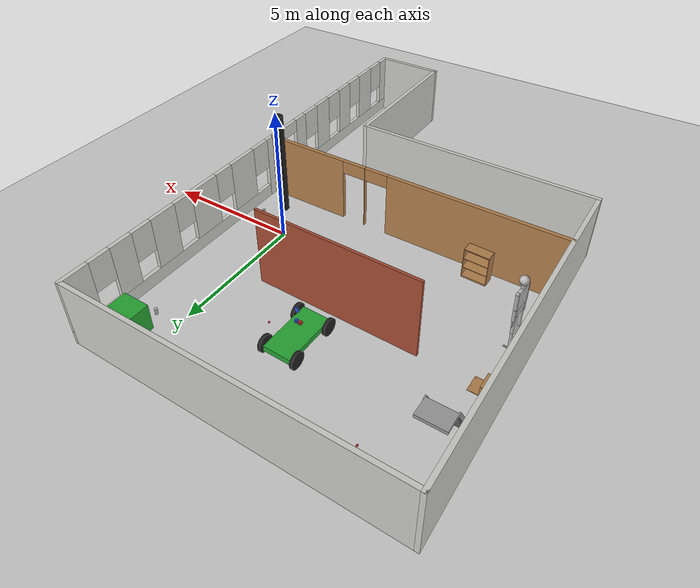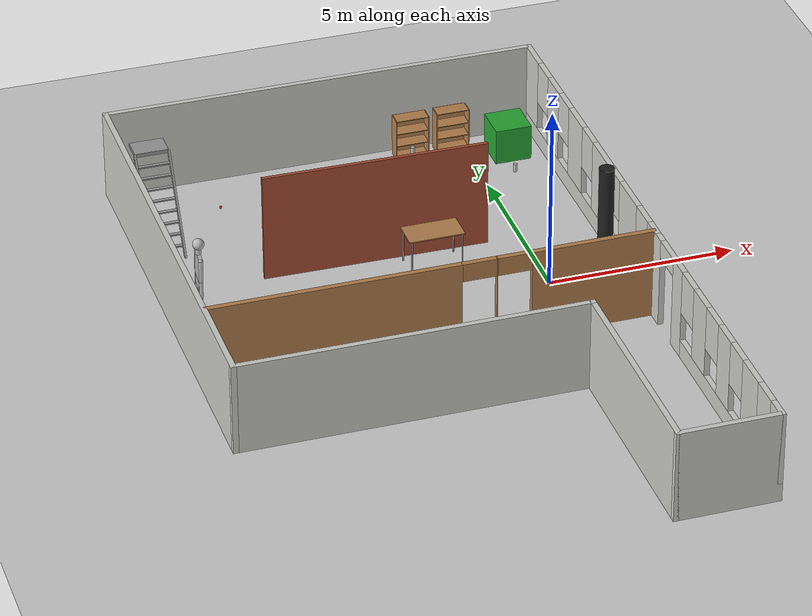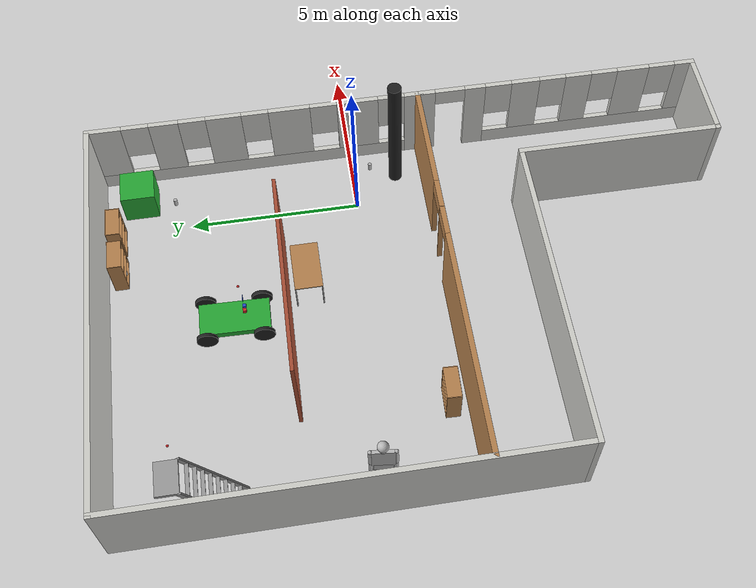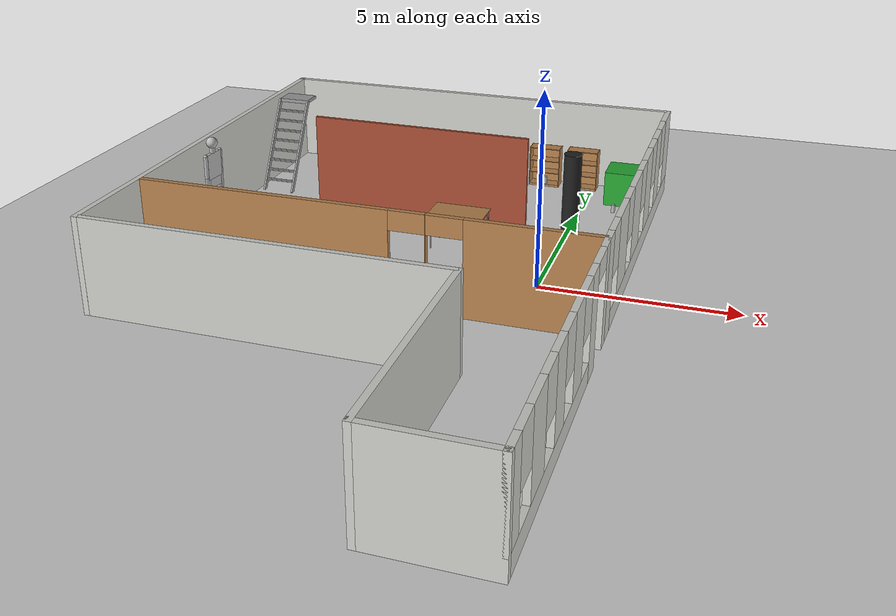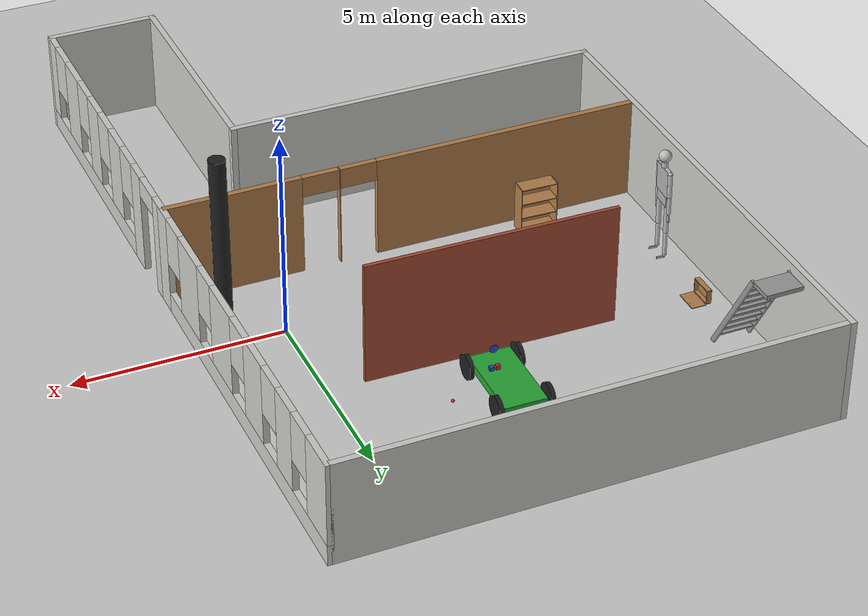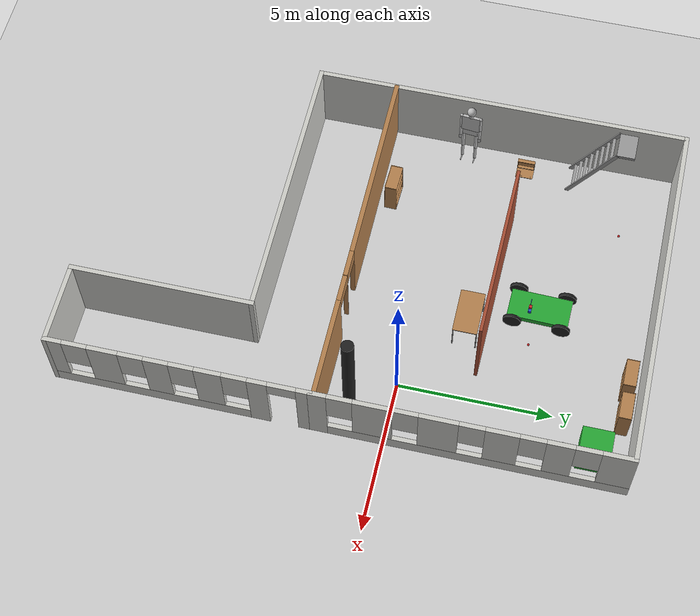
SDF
<sdf version="1.6">
 <world name="default">
  <plugin name="hello" filename="libhello.so"/>
  <light name="sun" type="directional">
   <pose>0 0 10 0 -0 0</pose>
   <diffuse>0.8 0.8 0.8 1</diffuse>
   <specular>0.2 0.2 0.2 1</specular>
   <attenuation>
    <range>1000</range>
    <constant>0.9</constant>
    <linear>0.01</linear>
    <quadratic>0.001</quadratic>
   </attenuation>
   <direction>-0.5 0.1 -0.9</direction>
  </light>
  <model name="ground_plane">
   <static>1</static>
   <link name="link">
    <collision name="collision">
     <geometry><plane><normal>0 0 1</normal><size>100 100</size></plane></geometry>
     <surface><friction><ode><mu>100</mu><mu2>50</mu2></ode></friction></surface>
    </collision>
    <visual name="visual">
     <cast_shadows>0</cast_shadows>
     <geometry><plane><normal>0 0 1</normal><size>100 100</size></plane></geometry>
     <material>
      <script><uri>file://media/materials/scripts/gazebo.material</uri><name>Gazebo/Grey</name></script>
     </material>
    </visual>
   </link>
  </model>
  <gravity>0 0 -9.8</gravity>
  <magnetic_field>6e-06 2.3e-05 -4.2e-05</magnetic_field>
  <atmosphere type="adiabatic"/>
  <physics name="default_physics" default="0" type="ode">
   <max_step_size>0.001</max_step_size>
   <real_time_factor>1</real_time_factor>
   <real_time_update_rate>1000</real_time_update_rate>
  </physics>
  <scene><ambient>0.4 0.4 0.4 1</ambient><background>0.7 0.7 0.7 1</background><shadows>1</shadows></scene>
  <spherical_coordinates>
   <surface_model>EARTH_WGS84</surface_model>
   <latitude_deg>0</latitude_deg>
   <longitude_deg>0</longitude_deg>
   <elevation>0</elevation>
   <heading_deg>0</heading_deg>
  </spherical_coordinates>
  <model name="bookshelf">
   <static>1</static>
   <link name="link">
    <inertial><mass>1</mass></inertial>
    <collision name="back">
     <pose>0 0.005 0.6 0 -0 0</pose>
     <geometry><box><size>0.9 0.01 1.2</size></box></geometry>
    </collision>
    <visual name="visual1">
     <pose>0 0.005 0.6 0 -0 0</pose>
     <geometry><box><size>0.9 0.01 1.2</size></box></geometry>
     <material>
      <script><uri>file://media/materials/scripts/gazebo.material</uri><name>Gazebo/Wood</name></script>
     </material>
    </visual>
    <collision name="left_side">
     <pose>0.45 -0.195 0.6 0 -0 0</pose>
     <geometry><box><size>0.02 0.4 1.2</size></box></geometry>
    </collision>
    <visual name="visual2">
     <pose>0.45 -0.195 0.6 0 -0 0</pose>
     <geometry><box><size>0.02 0.4 1.2</size></box></geometry>
     <material>
      <script><uri>file://media/materials/scripts/gazebo.material</uri><name>Gazebo/Wood</name></script>
     </material>
    </visual>
    <collision name="right_side">
     <pose>-0.45 -0.195 0.6 0 -0 0</pose>
     <geometry><box><size>0.02 0.4 1.2</size></box></geometry>
    </collision>
    <visual name="visual3">
     <pose>-0.45 -0.195 0.6 0 -0 0</pose>
     <geometry><box><size>0.02 0.4 1.2</size></box></geometry>
     <material>
      <script><uri>file://media/materials/scripts/gazebo.material</uri><name>Gazebo/Wood</name></script>
     </material>
    </visual>
    <collision name="bottom">
     <pose>0 -0.195 0.03 0 -0 0</pose>
     <geometry><box><size>0.88 0.4 0.06</size></box></geometry>
    </collision>
    <visual name="visual4">
     <pose>0 -0.195 0.03 0 -0 0</pose>
     <geometry><box><size>0.88 0.4 0.06</size></box></geometry>
     <material>
      <script><uri>file://media/materials/scripts/gazebo.material</uri><name>Gazebo/Wood</name></script>
     </material>
    </visual>
    <collision name="top">
     <pose>0 -0.195 1.19 0 -0 0</pose>
     <geometry><box><size>0.88 0.4 0.02</size></box></geometry>
    </collision>
    <visual name="visual5">
     <pose>0 -0.195 1.19 0 -0 0</pose>
     <geometry><box><size>0.88 0.4 0.02</size></box></geometry>
     <material>
      <script><uri>file://media/materials/scripts/gazebo.material</uri><name>Gazebo/Wood</name></script>
     </material>
    </visual>
    <collision name="low_shelf">
     <pose>0 -0.195 0.43 0 -0 0</pose>
     <geometry><box><size>0.88 0.4 0.02</size></box></geometry>
    </collision>
    <visual name="visual6">
     <pose>0 -0.195 0.43 0 -0 0</pose>
     <geometry><box><size>0.88 0.4 0.02</size></box></geometry>
     <material>
      <script><uri>file://media/materials/scripts/gazebo.material</uri><name>Gazebo/Wood</name></script>
     </material>
    </visual>
    <collision name="high_shelf">
     <pose>0 -0.195 0.8 0 -0 0</pose>
     <geometry><box><size>0.88 0.4 0.02</size></box></geometry>
    </collision>
    <visual name="visual7">
     <pose>0 -0.195 0.8 0 -0 0</pose>
     <geometry><box><size>0.88 0.4 0.02</size></box></geometry>
     <material>
      <script><uri>file://media/materials/scripts/gazebo.material</uri><name>Gazebo/Wood</name></script>
     </material>
    </visual>
   </link>
   <pose>-1.46178 7.33963 0 0 -0 0</pose>
  </model>
  <model name="Untitled">
   <link name="link_0">
    <inertial>
     <mass>1</mass>
     <inertia>
      <ixx>0.166667</ixx>
      <ixy>0</ixy>
      <ixz>0</ixz>
      <iyy>0.166667</iyy>
      <iyz>0</iyz>
      <izz>0.166667</izz>
     </inertia>
    </inertial>
    <visual name="visual">
     <geometry><box><size>1 1 1</size></box></geometry>
     <material>
      <lighting>1</lighting>
      <script><uri>file://media/materials/scripts/gazebo.material</uri><name>Gazebo/Green</name></script>
      <shader type="pixel"><normal_map>__default__</normal_map></shader>
      <ambient>1 0 0 1</ambient>
      <diffuse>0.7 0.7 0.7 1</diffuse>
      <specular>0.01 0.01 0.01 1</specular>
      <emissive>0 0 0 1</emissive>
     </material>
    </visual>
    <collision name="collision">
     <geometry><box><size>1 1 1</size></box></geometry>
     <surface>
      <friction>
       <ode><mu>1</mu><mu2>1</mu2><fdir1>0 0 0</fdir1><slip1>0</slip1><slip2>0</slip2></ode>
       <torsional>
        <coefficient>1</coefficient>
        <patch_radius>0</patch_radius>
        <surface_radius>0</surface_radius>
        <use_patch_radius>1</use_patch_radius>
        <ode><slip>0</slip></ode>
       </torsional>
      </friction>
      <bounce><restitution_coefficient>0</restitution_coefficient><threshold>1e+06</threshold></bounce>
      <contact>
       <collide_without_contact>0</collide_without_contact>
       <collide_without_contact_bitmask>1</collide_without_contact_bitmask>
       <collide_bitmask>1</collide_bitmask>
       <ode>
        <soft_cfm>0</soft_cfm>
        <soft_erp>0.2</soft_erp>
        <kp>1e+13</kp>
        <kd>1</kd>
        <max_vel>0.01</max_vel>
        <min_depth>0</min_depth>
       </ode>
       <bullet>
        <split_impulse>1</split_impulse>
        <split_impulse_penetration_threshold>-0.01</split_impulse_penetration_threshold>
        <soft_cfm>0</soft_cfm>
        <soft_erp>0.2</soft_erp>
        <kp>1e+13</kp>
        <kd>1</kd>
       </bullet>
      </contact>
     </surface>
    </collision>
   </link>
   <static>0</static>
   <pose>1.05703 6.46393 0.499995 0 -1e-05 0</pose>
  </model>
  <model name="unit_cylinder">
   <link name="link">
    <inertial>
     <mass>1</mass>
     <inertia><ixx>0.145833</ixx><ixy>0</ixy><ixz>0</ixz><iyy>0.145833</iyy><iyz>0</iyz><izz>0.125</izz></inertia>
    </inertial>
    <visual name="visual">
     <geometry><cylinder><radius>0.2</radius><length>4</length></cylinder></geometry>
     <material>
      <script><name>Gazebo/Black</name><uri>file://media/materials/scripts/gazebo.material</uri></script>
      <shader type="pixel"><normal_map>__default__</normal_map></shader>
      <ambient>1 0 0.5 1</ambient>
      <diffuse>0.7 0.7 0.7 1</diffuse>
      <specular>0.01 0.01 0.01 1</specular>
      <emissive>0 0 0 1</emissive>
     </material>
    </visual>
    <collision name="collision">
     <geometry><cylinder><radius>0.2</radius><length>4</length></cylinder></geometry>
     <surface>
      <friction>
       <ode><mu>1</mu><mu2>1</mu2><fdir1>0 0 0</fdir1><slip1>0</slip1><slip2>0</slip2></ode>
       <torsional>
        <coefficient>1</coefficient>
        <patch_radius>0</patch_radius>
        <surface_radius>0</surface_radius>
        <use_patch_radius>1</use_patch_radius>
        <ode><slip>0</slip></ode>
       </torsional>
      </friction>
      <bounce><restitution_coefficient>0</restitution_coefficient><threshold>1e+06</threshold></bounce>
      <contact>
       <collide_without_contact>0</collide_without_contact>
       <collide_without_contact_bitmask>1</collide_without_contact_bitmask>
       <collide_bitmask>1</collide_bitmask>
       <ode>
        <soft_cfm>0</soft_cfm>
        <soft_erp>0.2</soft_erp>
        <kp>1e+13</kp>
        <kd>1</kd>
        <max_vel>0.01</max_vel>
        <min_depth>0</min_depth>
       </ode>
       <bullet>
        <split_impulse>1</split_impulse>
        <split_impulse_penetration_threshold>-0.01</split_impulse_penetration_threshold>
        <soft_cfm>0</soft_cfm>
        <soft_erp>0.2</soft_erp>
        <kp>1e+13</kp>
        <kd>1</kd>
       </bullet>
      </contact>
     </surface>
    </collision>
   </link>
   <static>0</static>
   <pose>0.988926 -1.30848 1.99999 0 0 -0.008875</pose>
  </model>
  <model name="ragdoll">
   <pose>-9.10919 0.521164 1.39978 -0.000138 0.011625 -0.094994</pose>
   <link name="hip">
    <inertial>
     <inertia><ixx>0.1</ixx><ixy>0</ixy><ixz>0</ixz><iyy>0.1</iyy><iyz>0</iyz><izz>0.1</izz></inertia>
     <mass>10</mass>
    </inertial>
    <collision name="hip_geom">
     <pose>0 0 0.125 0 -0 0</pose>
     <geometry><box><size>0.1 0.5 0.25</size></box></geometry>
     <surface>
      <friction><ode><mu>-1</mu><mu2>-1</mu2><fdir1>0 0 0</fdir1><slip1>0</slip1><slip2>0</slip2></ode></friction>
      <bounce><restitution_coefficient>0</restitution_coefficient><threshold>100000</threshold></bounce>
      <contact>
       <ode>
        <soft_cfm>0</soft_cfm>
        <soft_erp>0.2</soft_erp>
        <kp>1e+12</kp>
        <kd>1</kd>
        <max_vel>0</max_vel>
        <min_depth>0.001</min_depth>
       </ode>
      </contact>
     </surface>
    </collision>
    <visual name="hip_geom_visual">
     <pose>0 0 0.125 0 -0 0</pose>
     <geometry><box><size>0.1 0.5 0.25</size></box></geometry>
    </visual>
    <gravity>0</gravity>
   </link>
   <link name="l_thigh_pan">
    <pose>0 0.22 0 0 -0 0</pose>
    <inertial>
     <inertia><ixx>0.01</ixx><ixy>0</ixy><ixz>0</ixz><iyy>0.01</iyy><iyz>0</iyz><izz>0.01</izz></inertia>
     <mass>1</mass>
    </inertial>
    <collision name="l_thigh_pan_geom">
     <pose>0 0 -0.03 0 -0 0</pose>
     <geometry><sphere><radius>0.06</radius></sphere></geometry>
     <surface>
      <friction><ode><mu>-1</mu><mu2>-1</mu2><fdir1>0 0 0</fdir1><slip1>0</slip1><slip2>0</slip2></ode></friction>
      <bounce><restitution_coefficient>0</restitution_coefficient><threshold>100000</threshold></bounce>
      <contact>
       <ode>
        <soft_cfm>0</soft_cfm>
        <soft_erp>0.2</soft_erp>
        <kp>1e+12</kp>
        <kd>1</kd>
        <max_vel>0</max_vel>
        <min_depth>0.001</min_depth>
       </ode>
      </contact>
     </surface>
    </collision>
    <visual name="l_thigh_pan_geom_visual">
     <pose>0 0 -0.03 0 -0 0</pose>
     <geometry><sphere><radius>0.06</radius></sphere></geometry>
    </visual>
    <gravity>0</gravity>
   </link>
   <link name="l_thigh_lift">
    <pose>0 0.22 0 0 -0 0</pose>
    <inertial>
     <inertia><ixx>0.05</ixx><ixy>0</ixy><ixz>0</ixz><iyy>0.05</iyy><iyz>0</iyz><izz>0.05</izz></inertia>
     <mass>5</mass>
    </inertial>
    <collision name="l_thigh_lift_geom">
     <pose>0 0 -0.35 0 -0 0</pose>
     <geometry><cylinder><radius>0.06</radius><length>0.7</length></cylinder></geometry>
     <surface>
      <friction><ode><mu>-1</mu><mu2>-1</mu2><fdir1>0 0 0</fdir1><slip1>0</slip1><slip2>0</slip2></ode></friction>
      <bounce><restitution_coefficient>0</restitution_coefficient><threshold>100000</threshold></bounce>
      <contact>
       <ode>
        <soft_cfm>0</soft_cfm>
        <soft_erp>0.2</soft_erp>
        <kp>1e+12</kp>
        <kd>1</kd>
        <max_vel>0</max_vel>
        <min_depth>0.001</min_depth>
       </ode>
      </contact>
     </surface>
    </collision>
    <visual name="l_thigh_lift_geom_visual">
     <pose>0 0 -0.35 0 -0 0</pose>
     <geometry><cylinder><radius>0.06</radius><length>0.7</length></cylinder></geometry>
    </visual>
    <gravity>0</gravity>
   </link>
   <link name="l_calf">
    <pose>0 0.22 -0.7 0 -0 0</pose>
    <inertial>
     <inertia><ixx>0.02</ixx><ixy>0</ixy><ixz>0</ixz><iyy>0.02</iyy><iyz>0</iyz><izz>0.02</izz></inertia>
     <mass>2</mass>
    </inertial>
    <collision name="l_calf_geom">
     <pose>0 0 -0.3 0 -0 0</pose>
     <geometry><cylinder><radius>0.05</radius><length>0.6</length></cylinder></geometry>
     <surface>
      <friction><ode><mu>-1</mu><mu2>-1</mu2><fdir1>0 0 0</fdir1><slip1>0</slip1><slip2>0</slip2></ode></friction>
      <bounce><restitution_coefficient>0</restitution_coefficient><threshold>100000</threshold></bounce>
      <contact>
       <ode>
        <soft_cfm>0</soft_cfm>
        <soft_erp>0.2</soft_erp>
        <kp>1e+12</kp>
        <kd>1</kd>
        <max_vel>0</max_vel>
        <min_depth>0.001</min_depth>
       </ode>
      </contact>
     </surface>
    </collision>
    <visual name="l_calf_geom_visual">
     <pose>0 0 -0.3 0 -0 0</pose>
     <geometry><cylinder><radius>0.05</radius><length>0.6</length></cylinder></geometry>
    </visual>
    <gravity>0</gravity>
   </link>
   <link name="l_ankle">
    <pose>0 0.22 -1.325 0 -0 0</pose>
    <inertial>
     <inertia><ixx>0.01</ixx><ixy>0</ixy><ixz>0</ixz><iyy>0.01</iyy><iyz>0</iyz><izz>0.01</izz></inertia>
     <mass>1</mass>
    </inertial>
    <collision name="l_ankle_geom">
     <geometry><sphere><radius>0.05</radius></sphere></geometry>
     <surface>
      <friction><ode><mu>-1</mu><mu2>-1</mu2><fdir1>0 0 0</fdir1><slip1>0</slip1><slip2>0</slip2></ode></friction>
      <bounce><restitution_coefficient>0</restitution_coefficient><threshold>100000</threshold></bounce>
      <contact>
       <ode>
        <soft_cfm>0</soft_cfm>
        <soft_erp>0.2</soft_erp>
        <kp>1e+12</kp>
        <kd>1</kd>
        <max_vel>0</max_vel>
        <min_depth>0.001</min_depth>
       </ode>
      </contact>
     </surface>
    </collision>
    <visual name="l_ankle_geom_visual"><geometry><sphere><radius>0.05</radius></sphere></geometry></visual>
    <gravity>0</gravity>
   </link>
   <link name="l_foot">
    <pose>0 0.22 -1.35 0 -0 0</pose>
    <inertial>
     <pose>0.1 0 0 0 -0 0</pose>
     <inertia><ixx>0.01</ixx><ixy>0</ixy><ixz>0</ixz><iyy>0.01</iyy><iyz>0</iyz><izz>0.01</izz></inertia>
     <mass>1</mass>
    </inertial>
    <collision name="l_foot_geom">
     <pose>0.1 0 -0.025 0 -0 0</pose>
     <geometry><box><size>0.2 0.03 0.05</size></box></geometry>
     <surface>
      <friction><ode><mu>-1</mu><mu2>-1</mu2><fdir1>0 0 0</fdir1><slip1>0</slip1><slip2>0</slip2></ode></friction>
      <bounce><restitution_coefficient>0</restitution_coefficient><threshold>100000</threshold></bounce>
      <contact>
       <ode>
        <soft_cfm>0</soft_cfm>
        <soft_erp>0.2</soft_erp>
        <kp>1e+12</kp>
        <kd>1</kd>
        <max_vel>0</max_vel>
        <min_depth>0.001</min_depth>
       </ode>
      </contact>
     </surface>
    </collision>
    <visual name="l_foot_geom_visual">
     <pose>0.1 0 -0.025 0 -0 0</pose>
     <geometry><box><size>0.2 0.03 0.05</size></box></geometry>
    </visual>
   </link>
   <link name="r_thigh_pan">
    <pose>0 -0.22 0 0 -0 0</pose>
    <inertial>
     <inertia><ixx>0.01</ixx><ixy>0</ixy><ixz>0</ixz><iyy>0.01</iyy><iyz>0</iyz><izz>0.01</izz></inertia>
     <mass>1</mass>
    </inertial>
    <collision name="r_thigh_pan_geom">
     <pose>0 0 -0.03 0 -0 0</pose>
     <geometry><sphere><radius>0.06</radius></sphere></geometry>
     <surface>
      <friction><ode><mu>-1</mu><mu2>-1</mu2><fdir1>0 0 0</fdir1><slip1>0</slip1><slip2>0</slip2></ode></friction>
      <bounce><restitution_coefficient>0</restitution_coefficient><threshold>100000</threshold></bounce>
      <contact>
       <ode>
        <soft_cfm>0</soft_cfm>
        <soft_erp>0.2</soft_erp>
        <kp>1e+12</kp>
        <kd>1</kd>
        <max_vel>0</max_vel>
        <min_depth>0.001</min_depth>
       </ode>
      </contact>
     </surface>
    </collision>
    <visual name="r_thigh_pan_geom_visual">
     <pose>0 0 -0.03 0 -0 0</pose>
     <geometry><sphere><radius>0.06</radius></sphere></geometry>
    </visual>
    <gravity>0</gravity>
   </link>
   <link name="r_thigh_lift">
    <pose>0 -0.22 0 0 -0 0</pose>
    <inertial>
     <inertia><ixx>0.05</ixx><ixy>0</ixy><ixz>0</ixz><iyy>0.05</iyy><iyz>0</iyz><izz>0.05</izz></inertia>
     <mass>5</mass>
    </inertial>
    <collision name="r_thigh_lift_geom">
     <pose>0 0 -0.35 0 -0 0</pose>
     <geometry><cylinder><radius>0.06</radius><length>0.7</length></cylinder></geometry>
     <surface>
      <friction><ode><mu>-1</mu><mu2>-1</mu2><fdir1>0 0 0</fdir1><slip1>0</slip1><slip2>0</slip2></ode></friction>
      <bounce><restitution_coefficient>0</restitution_coefficient><threshold>100000</threshold></bounce>
      <contact>
       <ode>
        <soft_cfm>0</soft_cfm>
        <soft_erp>0.2</soft_erp>
        <kp>1e+12</kp>
        <kd>1</kd>
        <max_vel>0</max_vel>
        <min_depth>0.001</min_depth>
       </ode>
      </contact>
     </surface>
    </collision>
    <visual name="r_thigh_lift_geom_visual">
     <pose>0 0 -0.35 0 -0 0</pose>
     <geometry><cylinder><radius>0.06</radius><length>0.7</length></cylinder></geometry>
    </visual>
    <gravity>0</gravity>
   </link>
   <link name="r_calf">
    <pose>0 -0.22 -0.7 0 -0 0</pose>
    <inertial>
     <inertia><ixx>0.02</ixx><ixy>0</ixy><ixz>0</ixz><iyy>0.02</iyy><iyz>0</iyz><izz>0.02</izz></inertia>
     <mass>2</mass>
    </inertial>
    <collision name="r_calf_geom">
     <pose>0 0 -0.3 0 -0 0</pose>
     <geometry><cylinder><radius>0.05</radius><length>0.6</length></cylinder></geometry>
     <surface>
      <friction><ode><mu>-1</mu><mu2>-1</mu2><fdir1>0 0 0</fdir1><slip1>0</slip1><slip2>0</slip2></ode></friction>
      <bounce><restitution_coefficient>0</restitution_coefficient><threshold>100000</threshold></bounce>
      <contact>
       <ode>
        <soft_cfm>0</soft_cfm>
        <soft_erp>0.2</soft_erp>
        <kp>1e+12</kp>
        <kd>1</kd>
        <max_vel>0</max_vel>
        <min_depth>0.001</min_depth>
       </ode>
      </contact>
     </surface>
    </collision>
    <visual name="r_calf_geom_visual">
     <pose>0 0 -0.3 0 -0 0</pose>
     <geometry><cylinder><radius>0.05</radius><length>0.6</length></cylinder></geometry>
    </visual>
    <gravity>0</gravity>
   </link>
   <link name="r_ankle">
    <pose>0 -0.22 -1.325 0 -0 0</pose>
    <inertial>
     <inertia><ixx>0.01</ixx><ixy>0</ixy><ixz>0</ixz><iyy>0.01</iyy><iyz>0</iyz><izz>0.01</izz></inertia>
     <mass>1</mass>
    </inertial>
    <collision name="r_ankle_geom">
     <geometry><sphere><radius>0.05</radius></sphere></geometry>
     <surface>
      <friction><ode><mu>-1</mu><mu2>-1</mu2><fdir1>0 0 0</fdir1><slip1>0</slip1><slip2>0</slip2></ode></friction>
      <bounce><restitution_coefficient>0</restitution_coefficient><threshold>100000</threshold></bounce>
      <contact>
       <ode>
        <soft_cfm>0</soft_cfm>
        <soft_erp>0.2</soft_erp>
        <kp>1e+12</kp>
        <kd>1</kd>
        <max_vel>0</max_vel>
        <min_depth>0.001</min_depth>
       </ode>
      </contact>
     </surface>
    </collision>
    <visual name="r_ankle_geom_visual"><geometry><sphere><radius>0.05</radius></sphere></geometry></visual>
    <gravity>0</gravity>
   </link>
   <link name="r_foot">
    <pose>0 -0.22 -1.35 0 -0 0</pose>
    <inertial>
     <pose>0.1 0 0 0 -0 0</pose>
     <inertia><ixx>0.01</ixx><ixy>0</ixy><ixz>0</ixz><iyy>0.01</iyy><iyz>0</iyz><izz>0.01</izz></inertia>
     <mass>1</mass>
    </inertial>
    <collision name="r_foot_geom">
     <pose>0.1 0 -0.025 0 -0 0</pose>
     <geometry><box><size>0.2 0.03 0.05</size></box></geometry>
     <surface>
      <friction><ode><mu>-1</mu><mu2>-1</mu2><fdir1>0 0 0</fdir1><slip1>0</slip1><slip2>0</slip2></ode></friction>
      <bounce><restitution_coefficient>0</restitution_coefficient><threshold>100000</threshold></bounce>
      <contact>
       <ode>
        <soft_cfm>0</soft_cfm>
        <soft_erp>0.2</soft_erp>
        <kp>1e+12</kp>
        <kd>1</kd>
        <max_vel>0</max_vel>
        <min_depth>0.001</min_depth>
       </ode>
      </contact>
     </surface>
    </collision>
    <visual name="r_foot_geom_visual">
     <pose>0.1 0 -0.025 0 -0 0</pose>
     <geometry><box><size>0.2 0.03 0.05</size></box></geometry>
    </visual>
   </link>
   <link name="torso">
    <pose>0 0 0.25 0 -0 0</pose>
    <inertial>
     <inertia><ixx>0.3</ixx><ixy>0</ixy><ixz>0</ixz><iyy>0.3</iyy><iyz>0</iyz><izz>0.3</izz></inertia>
     <mass>30</mass>
    </inertial>
    <collision name="torso_geom">
     <pose>0 0 0.35 0 -0 0</pose>
     <geometry><box><size>0.1 0.6 0.7</size></box></geometry>
     <surface>
      <friction><ode><mu>-1</mu><mu2>-1</mu2><fdir1>0 0 0</fdir1><slip1>0</slip1><slip2>0</slip2></ode></friction>
      <bounce><restitution_coefficient>0</restitution_coefficient><threshold>100000</threshold></bounce>
      <contact>
       <ode>
        <soft_cfm>0</soft_cfm>
        <soft_erp>0.2</soft_erp>
        <kp>1e+12</kp>
        <kd>1</kd>
        <max_vel>0</max_vel>
        <min_depth>0.001</min_depth>
       </ode>
      </contact>
     </surface>
    </collision>
    <visual name="torso_geom_visual">
     <pose>0 0 0.35 0 -0 0</pose>
     <geometry><box><size>0.1 0.6 0.7</size></box></geometry>
    </visual>
    <gravity>0</gravity>
   </link>
   <link name="l_shoulder">
    <pose>0 0.3275 0.9225 0 -0 0</pose>
    <inertial>
     <inertia><ixx>0.01</ixx><ixy>0</ixy><ixz>0</ixz><iyy>0.01</iyy><iyz>0</iyz><izz>0.01</izz></inertia>
     <mass>1</mass>
    </inertial>
    <collision name="l_shoulder_geom">
     <geometry><sphere><radius>0.055</radius></sphere></geometry>
     <surface>
      <friction><ode><mu>-1</mu><mu2>-1</mu2><fdir1>0 0 0</fdir1><slip1>0</slip1><slip2>0</slip2></ode></friction>
      <bounce><restitution_coefficient>0</restitution_coefficient><threshold>100000</threshold></bounce>
      <contact>
       <ode>
        <soft_cfm>0</soft_cfm>
        <soft_erp>0.2</soft_erp>
        <kp>1e+12</kp>
        <kd>1</kd>
        <max_vel>0</max_vel>
        <min_depth>0.001</min_depth>
       </ode>
      </contact>
     </surface>
    </collision>
    <visual name="l_shoulder_geom_visual"><geometry><sphere><radius>0.055</radius></sphere></geometry></visual>
    <gravity>0</gravity>
   </link>
   <link name="l_upper_arm">
    <pose>0 0.3275 0.9225 0 -0 0</pose>
    <inertial>
     <inertia><ixx>0.02</ixx><ixy>0</ixy><ixz>0</ixz><iyy>0.02</iyy><iyz>0</iyz><izz>0.02</izz></inertia>
     <mass>2</mass>
    </inertial>
    <collision name="l_upper_arm_geom">
     <pose>0 0 -0.3 0 -0 0</pose>
     <geometry><cylinder><radius>0.055</radius><length>0.6</length></cylinder></geometry>
     <surface>
      <friction><ode><mu>-1</mu><mu2>-1</mu2><fdir1>0 0 0</fdir1><slip1>0</slip1><slip2>0</slip2></ode></friction>
      <bounce><restitution_coefficient>0</restitution_coefficient><threshold>100000</threshold></bounce>
      <contact>
       <ode>
        <soft_cfm>0</soft_cfm>
        <soft_erp>0.2</soft_erp>
        <kp>1e+12</kp>
        <kd>1</kd>
        <max_vel>0</max_vel>
        <min_depth>0.001</min_depth>
       </ode>
      </contact>
     </surface>
    </collision>
    <visual name="l_upper_arm_geom_visual">
     <pose>0 0 -0.3 0 -0 0</pose>
     <geometry><cylinder><radius>0.055</radius><length>0.6</length></cylinder></geometry>
    </visual>
    <gravity>0</gravity>
   </link>
   <link name="l_forearm">
    <pose>0 0.3275 0.3225 0 -0 0</pose>
    <inertial>
     <inertia><ixx>0.01</ixx><ixy>0</ixy><ixz>0</ixz><iyy>0.01</iyy><iyz>0</iyz><izz>0.01</izz></inertia>
     <mass>1</mass>
    </inertial>
    <collision name="l_forearm_geom">
     <pose>0 0 -0.225 0 -0 0</pose>
     <geometry><cylinder><radius>0.05</radius><length>0.45</length></cylinder></geometry>
     <surface>
      <friction><ode><mu>-1</mu><mu2>-1</mu2><fdir1>0 0 0</fdir1><slip1>0</slip1><slip2>0</slip2></ode></friction>
      <bounce><restitution_coefficient>0</restitution_coefficient><threshold>100000</threshold></bounce>
      <contact>
       <ode>
        <soft_cfm>0</soft_cfm>
        <soft_erp>0.2</soft_erp>
        <kp>1e+12</kp>
        <kd>1</kd>
        <max_vel>0</max_vel>
        <min_depth>0.001</min_depth>
       </ode>
      </contact>
     </surface>
    </collision>
    <visual name="l_forearm_geom_visual">
     <pose>0 0 -0.225 0 -0 0</pose>
     <geometry><cylinder><radius>0.05</radius><length>0.45</length></cylinder></geometry>
    </visual>
    <gravity>0</gravity>
   </link>
   <link name="l_wrist">
    <pose>0 0.3275 -0.1425 0 -0 0</pose>
    <inertial>
     <inertia><ixx>0.01</ixx><ixy>0</ixy><ixz>0</ixz><iyy>0.01</iyy><iyz>0</iyz><izz>0.01</izz></inertia>
     <mass>1</mass>
    </inertial>
    <collision name="l_wrist_geom">
     <geometry><sphere><radius>0.03</radius></sphere></geometry>
     <surface>
      <friction><ode><mu>-1</mu><mu2>-1</mu2><fdir1>0 0 0</fdir1><slip1>0</slip1><slip2>0</slip2></ode></friction>
      <bounce><restitution_coefficient>0</restitution_coefficient><threshold>100000</threshold></bounce>
      <contact>
       <ode>
        <soft_cfm>0</soft_cfm>
        <soft_erp>0.2</soft_erp>
        <kp>1e+12</kp>
        <kd>1</kd>
        <max_vel>0</max_vel>
        <min_depth>0.001</min_depth>
       </ode>
      </contact>
     </surface>
    </collision>
    <visual name="l_wrist_geom_visual"><geometry><sphere><radius>0.03</radius></sphere></geometry></visual>
    <gravity>0</gravity>
   </link>
   <link name="l_hand">
    <pose>0 0.3275 -0.1575 0 -0 0</pose>
    <inertial>
     <inertia><ixx>0.01</ixx><ixy>0</ixy><ixz>0</ixz><iyy>0.01</iyy><iyz>0</iyz><izz>0.01</izz></inertia>
     <mass>1</mass>
    </inertial>
    <collision name="l_hand_geom">
     <pose>0 0 -0.1 0 -0 0</pose>
     <geometry><box><size>0.03 0.1 0.2</size></box></geometry>
     <surface>
      <friction><ode><mu>-1</mu><mu2>-1</mu2><fdir1>0 0 0</fdir1><slip1>0</slip1><slip2>0</slip2></ode></friction>
      <bounce><restitution_coefficient>0</restitution_coefficient><threshold>100000</threshold></bounce>
      <contact>
       <ode>
        <soft_cfm>0</soft_cfm>
        <soft_erp>0.2</soft_erp>
        <kp>1e+12</kp>
        <kd>1</kd>
        <max_vel>0</max_vel>
        <min_depth>0.001</min_depth>
       </ode>
      </contact>
     </surface>
    </collision>
    <visual name="l_hand_geom_visual">
     <pose>0 0 -0.1 0 -0 0</pose>
     <geometry><box><size>0.03 0.1 0.2</size></box></geometry>
    </visual>
    <gravity>0</gravity>
   </link>
   <link name="neck">
    <pose>0 0 0.95 0 -0 0</pose>
    <inertial>
     <inertia><ixx>0.01</ixx><ixy>0</ixy><ixz>0</ixz><iyy>0.01</iyy><iyz>0</iyz><izz>0.01</izz></inertia>
     <mass>1</mass>
    </inertial>
    <collision name="neck_geom">
     <pose>0 0 0.1 0 -0 0</pose>
     <geometry><cylinder><radius>0.075</radius><length>0.2</length></cylinder></geometry>
     <surface>
      <friction><ode><mu>-1</mu><mu2>-1</mu2><fdir1>0 0 0</fdir1><slip1>0</slip1><slip2>0</slip2></ode></friction>
      <bounce><restitution_coefficient>0</restitution_coefficient><threshold>100000</threshold></bounce>
      <contact>
       <ode>
        <soft_cfm>0</soft_cfm>
        <soft_erp>0.2</soft_erp>
        <kp>1e+12</kp>
        <kd>1</kd>
        <max_vel>0</max_vel>
        <min_depth>0.001</min_depth>
       </ode>
      </contact>
     </surface>
    </collision>
    <visual name="neck_geom_visual">
     <pose>0 0 0.1 0 -0 0</pose>
     <geometry><cylinder><radius>0.075</radius><length>0.2</length></cylinder></geometry>
    </visual>
    <gravity>0</gravity>
   </link>
   <link name="head">
    <pose>0 0 1.225 0 -0 0</pose>
    <inertial>
     <inertia><ixx>0.1</ixx><ixy>0</ixy><ixz>0</ixz><iyy>0.1</iyy><iyz>0</iyz><izz>0.1</izz></inertia>
     <mass>10</mass>
    </inertial>
    <collision name="head_geom">
     <geometry><sphere><radius>0.15</radius></sphere></geometry>
     <surface>
      <friction><ode><mu>-1</mu><mu2>-1</mu2><fdir1>0 0 0</fdir1><slip1>0</slip1><slip2>0</slip2></ode></friction>
      <bounce><restitution_coefficient>0</restitution_coefficient><threshold>100000</threshold></bounce>
      <contact>
       <ode>
        <soft_cfm>0</soft_cfm>
        <soft_erp>0.2</soft_erp>
        <kp>1e+12</kp>
        <kd>1</kd>
        <max_vel>0</max_vel>
        <min_depth>0.001</min_depth>
       </ode>
      </contact>
     </surface>
    </collision>
    <visual name="head_geom_visual"><geometry><sphere><radius>0.15</radius></sphere></geometry></visual>
    <gravity>0</gravity>
   </link>
   <link name="r_shoulder">
    <pose>0 -0.3275 0.9225 0 -0 0</pose>
    <inertial>
     <inertia><ixx>0.01</ixx><ixy>0</ixy><ixz>0</ixz><iyy>0.01</iyy><iyz>0</iyz><izz>0.01</izz></inertia>
     <mass>1</mass>
    </inertial>
    <collision name="r_shoulder_geom">
     <geometry><sphere><radius>0.055</radius></sphere></geometry>
     <surface>
      <friction><ode><mu>-1</mu><mu2>-1</mu2><fdir1>0 0 0</fdir1><slip1>0</slip1><slip2>0</slip2></ode></friction>
      <bounce><restitution_coefficient>0</restitution_coefficient><threshold>100000</threshold></bounce>
      <contact>
       <ode>
        <soft_cfm>0</soft_cfm>
        <soft_erp>0.2</soft_erp>
        <kp>1e+12</kp>
        <kd>1</kd>
        <max_vel>0</max_vel>
        <min_depth>0.001</min_depth>
       </ode>
      </contact>
     </surface>
    </collision>
    <visual name="r_shoulder_geom_visual"><geometry><sphere><radius>0.055</radius></sphere></geometry></visual>
    <gravity>0</gravity>
   </link>
   <link name="r_upper_arm">
    <pose>0 -0.3275 0.9225 0 -0 0</pose>
    <inertial>
     <inertia><ixx>0.02</ixx><ixy>0</ixy><ixz>0</ixz><iyy>0.02</iyy><iyz>0</iyz><izz>0.02</izz></inertia>
     <mass>2</mass>
    </inertial>
    <collision name="r_upper_arm_geom">
     <pose>0 0 -0.3 0 -0 0</pose>
     <geometry><cylinder><radius>0.055</radius><length>0.6</length></cylinder></geometry>
     <surface>
      <friction><ode><mu>-1</mu><mu2>-1</mu2><fdir1>0 0 0</fdir1><slip1>0</slip1><slip2>0</slip2></ode></friction>
      <bounce><restitution_coefficient>0</restitution_coefficient><threshold>100000</threshold></bounce>
      <contact>
       <ode>
        <soft_cfm>0</soft_cfm>
        <soft_erp>0.2</soft_erp>
        <kp>1e+12</kp>
        <kd>1</kd>
        <max_vel>0</max_vel>
        <min_depth>0.001</min_depth>
       </ode>
      </contact>
     </surface>
    </collision>
    <visual name="r_upper_arm_geom_visual">
     <pose>0 0 -0.3 0 -0 0</pose>
     <geometry><cylinder><radius>0.055</radius><length>0.6</length></cylinder></geometry>
    </visual>
    <gravity>0</gravity>
   </link>
   <link name="r_forearm">
    <pose>0 -0.3275 0.3225 0 -0 0</pose>
    <inertial>
     <inertia><ixx>0.01</ixx><ixy>0</ixy><ixz>0</ixz><iyy>0.01</iyy><iyz>0</iyz><izz>0.01</izz></inertia>
     <mass>1</mass>
    </inertial>
    <collision name="r_forearm_geom">
     <pose>0 0 -0.225 0 -0 0</pose>
     <geometry><cylinder><radius>0.05</radius><length>0.45</length></cylinder></geometry>
     <surface>
      <friction><ode><mu>-1</mu><mu2>-1</mu2><fdir1>0 0 0</fdir1><slip1>0</slip1><slip2>0</slip2></ode></friction>
      <bounce><restitution_coefficient>0</restitution_coefficient><threshold>100000</threshold></bounce>
      <contact>
       <ode>
        <soft_cfm>0</soft_cfm>
        <soft_erp>0.2</soft_erp>
        <kp>1e+12</kp>
        <kd>1</kd>
        <max_vel>0</max_vel>
        <min_depth>0.001</min_depth>
       </ode>
      </contact>
     </surface>
    </collision>
    <visual name="r_forearm_geom_visual">
     <pose>0 0 -0.225 0 -0 0</pose>
     <geometry><cylinder><radius>0.05</radius><length>0.45</length></cylinder></geometry>
    </visual>
    <gravity>0</gravity>
   </link>
   <link name="r_wrist">
    <pose>0 -0.3275 -0.1425 0 -0 0</pose>
    <inertial>
     <inertia><ixx>0.01</ixx><ixy>0</ixy><ixz>0</ixz><iyy>0.01</iyy><iyz>0</iyz><izz>0.01</izz></inertia>
     <mass>1</mass>
    </inertial>
    <collision name="r_wrist_geom">
     <geometry><sphere><radius>0.03</radius></sphere></geometry>
     <surface>
      <friction><ode><mu>-1</mu><mu2>-1</mu2><fdir1>0 0 0</fdir1><slip1>0</slip1><slip2>0</slip2></ode></friction>
      <bounce><restitution_coefficient>0</restitution_coefficient><threshold>100000</threshold></bounce>
      <contact>
       <ode>
        <soft_cfm>0</soft_cfm>
        <soft_erp>0.2</soft_erp>
        <kp>1e+12</kp>
        <kd>1</kd>
        <max_vel>0</max_vel>
        <min_depth>0.001</min_depth>
       </ode>
      </contact>
     </surface>
    </collision>
    <visual name="r_wrist_geom_visual"><geometry><sphere><radius>0.03</radius></sphere></geometry></visual>
    <gravity>0</gravity>
   </link>
   <link name="r_hand">
    <pose>0 -0.3275 -0.1575 0 -0 0</pose>
    <inertial>
     <inertia><ixx>0.01</ixx><ixy>0</ixy><ixz>0</ixz><iyy>0.01</iyy><iyz>0</iyz><izz>0.01</izz></inertia>
     <mass>1</mass>
    </inertial>
    <collision name="r_hand_geom">
     <pose>0 0 -0.1 0 -0 0</pose>
     <geometry><box><size>0.03 0.1 0.2</size></box></geometry>
     <surface>
      <friction><ode><mu>-1</mu><mu2>-1</mu2><fdir1>0 0 0</fdir1><slip1>0</slip1><slip2>0</slip2></ode></friction>
      <bounce><restitution_coefficient>0</restitution_coefficient><threshold>100000</threshold></bounce>
      <contact>
       <ode>
        <soft_cfm>0</soft_cfm>
        <soft_erp>0.2</soft_erp>
        <kp>1e+12</kp>
        <kd>1</kd>
        <max_vel>0</max_vel>
        <min_depth>0.001</min_depth>
       </ode>
      </contact>
     </surface>
    </collision>
    <visual name="r_hand_geom_visual">
     <pose>0 0 -0.1 0 -0 0</pose>
     <geometry><box><size>0.03 0.1 0.2</size></box></geometry>
    </visual>
    <gravity>0</gravity>
   </link>
   <joint name="l_thigh_pan_joint" type="revolute">
    <parent>hip</parent>
    <child>l_thigh_pan</child>
    <axis>
     <dynamics>
      <damping>0</damping>
      <friction>0</friction>
      <spring_reference>0</spring_reference>
      <spring_stiffness>0</spring_stiffness>
     </dynamics>
     <limit><lower>-1.5708</lower><upper>1.5708</upper><effort>0</effort><velocity>0</velocity></limit>
     <xyz>0 0 1</xyz>
     <use_parent_model_frame>1</use_parent_model_frame>
    </axis>
   </joint>
   <joint name="l_thigh_lift_joint" type="revolute">
    <parent>l_thigh_pan</parent>
    <child>l_thigh_lift</child>
    <axis>
     <dynamics>
      <damping>0</damping>
      <friction>0</friction>
      <spring_reference>0</spring_reference>
      <spring_stiffness>0</spring_stiffness>
     </dynamics>
     <limit><lower>-1.5708</lower><upper>1.5708</upper><effort>0</effort><velocity>0</velocity></limit>
     <xyz>0 1 0</xyz>
     <use_parent_model_frame>1</use_parent_model_frame>
    </axis>
   </joint>
   <joint name="l_calf_joint" type="revolute">
    <parent>l_thigh_lift</parent>
    <child>l_calf</child>
    <axis>
     <dynamics>
      <damping>0</damping>
      <friction>0</friction>
      <spring_reference>0</spring_reference>
      <spring_stiffness>0</spring_stiffness>
     </dynamics>
     <limit><lower>-1.5708</lower><upper>1.5708</upper><effort>0</effort><velocity>0</velocity></limit>
     <xyz>0 1 0</xyz>
     <use_parent_model_frame>1</use_parent_model_frame>
    </axis>
   </joint>
   <joint name="l_ankle_joint" type="revolute">
    <parent>l_calf</parent>
    <child>l_ankle</child>
    <axis>
     <dynamics>
      <damping>0</damping>
      <friction>0</friction>
      <spring_reference>0</spring_reference>
      <spring_stiffness>0</spring_stiffness>
     </dynamics>
     <limit><lower>-1.5708</lower><upper>1.5708</upper><effort>0</effort><velocity>0</velocity></limit>
     <xyz>0 1 0</xyz>
     <use_parent_model_frame>1</use_parent_model_frame>
    </axis>
   </joint>
   <joint name="l_foot_joint" type="revolute">
    <parent>l_ankle</parent>
    <child>l_foot</child>
    <axis>
     <dynamics>
      <damping>0</damping>
      <friction>0</friction>
      <spring_reference>0</spring_reference>
      <spring_stiffness>0</spring_stiffness>
     </dynamics>
     <limit><lower>-1.5708</lower><upper>1.5708</upper><effort>0</effort><velocity>0</velocity></limit>
     <xyz>1 0 0</xyz>
     <use_parent_model_frame>1</use_parent_model_frame>
    </axis>
   </joint>
   <joint name="r_thigh_pan_joint" type="revolute">
    <parent>hip</parent>
    <child>r_thigh_pan</child>
    <axis>
     <dynamics>
      <damping>0</damping>
      <friction>0</friction>
      <spring_reference>0</spring_reference>
      <spring_stiffness>0</spring_stiffness>
     </dynamics>
     <limit><lower>-1.5708</lower><upper>1.5708</upper><effort>0</effort><velocity>0</velocity></limit>
     <xyz>0 0 1</xyz>
     <use_parent_model_frame>1</use_parent_model_frame>
    </axis>
   </joint>
   <joint name="r_thigh_lift_joint" type="revolute">
    <parent>r_thigh_pan</parent>
    <child>r_thigh_lift</child>
    <axis>
     <dynamics>
      <damping>0</damping>
      <friction>0</friction>
      <spring_reference>0</spring_reference>
      <spring_stiffness>0</spring_stiffness>
     </dynamics>
     <limit><lower>-1.5708</lower><upper>1.5708</upper><effort>0</effort><velocity>0</velocity></limit>
     <xyz>0 1 0</xyz>
     <use_parent_model_frame>1</use_parent_model_frame>
    </axis>
   </joint>
   <joint name="r_calf_joint" type="revolute">
    <parent>r_thigh_lift</parent>
    <child>r_calf</child>
    <axis>
     <dynamics>
      <damping>0</damping>
      <friction>0</friction>
      <spring_reference>0</spring_reference>
      <spring_stiffness>0</spring_stiffness>
     </dynamics>
     <limit><lower>-1.5708</lower><upper>1.5708</upper><effort>0</effort><velocity>0</velocity></limit>
     <xyz>0 1 0</xyz>
     <use_parent_model_frame>1</use_parent_model_frame>
    </axis>
   </joint>
   <joint name="r_ankle_joint" type="revolute">
    <parent>r_calf</parent>
    <child>r_ankle</child>
    <axis>
     <dynamics>
      <damping>0</damping>
      <friction>0</friction>
      <spring_reference>0</spring_reference>
      <spring_stiffness>0</spring_stiffness>
     </dynamics>
     <limit><lower>-1.5708</lower><upper>1.5708</upper><effort>0</effort><velocity>0</velocity></limit>
     <xyz>0 1 0</xyz>
     <use_parent_model_frame>1</use_parent_model_frame>
    </axis>
   </joint>
   <joint name="r_foot_joint" type="revolute">
    <parent>r_ankle</parent>
    <child>r_foot</child>
    <axis>
     <dynamics>
      <damping>0</damping>
      <friction>0</friction>
      <spring_reference>0</spring_reference>
      <spring_stiffness>0</spring_stiffness>
     </dynamics>
     <limit><lower>-1.5708</lower><upper>1.5708</upper><effort>0</effort><velocity>0</velocity></limit>
     <xyz>1 0 0</xyz>
     <use_parent_model_frame>1</use_parent_model_frame>
    </axis>
   </joint>
   <joint name="torso_joint" type="revolute">
    <parent>hip</parent>
    <child>torso</child>
    <axis>
     <dynamics>
      <damping>0</damping>
      <friction>0</friction>
      <spring_reference>0</spring_reference>
      <spring_stiffness>0</spring_stiffness>
     </dynamics>
     <limit><lower>-1.5708</lower><upper>1.5708</upper><effort>0</effort><velocity>0</velocity></limit>
     <xyz>0 1 0</xyz>
     <use_parent_model_frame>1</use_parent_model_frame>
    </axis>
   </joint>
   <joint name="l_shoulder_joint" type="revolute">
    <parent>torso</parent>
    <child>l_shoulder</child>
    <axis>
     <dynamics>
      <damping>0</damping>
      <friction>0</friction>
      <spring_reference>0</spring_reference>
      <spring_stiffness>0</spring_stiffness>
     </dynamics>
     <limit><lower>-1.5708</lower><upper>1.5708</upper><effort>0</effort><velocity>0</velocity></limit>
     <xyz>1 0 0</xyz>
     <use_parent_model_frame>1</use_parent_model_frame>
    </axis>
   </joint>
   <joint name="l_upper_arm_joint" type="revolute">
    <parent>l_shoulder</parent>
    <child>l_upper_arm</child>
    <axis>
     <dynamics>
      <damping>0</damping>
      <friction>0</friction>
      <spring_reference>0</spring_reference>
      <spring_stiffness>0</spring_stiffness>
     </dynamics>
     <limit><lower>-1.5708</lower><upper>1.5708</upper><effort>0</effort><velocity>0</velocity></limit>
     <xyz>0 1 0</xyz>
     <use_parent_model_frame>1</use_parent_model_frame>
    </axis>
   </joint>
   <joint name="l_forearm_joint" type="revolute">
    <parent>l_upper_arm</parent>
    <child>l_forearm</child>
    <axis>
     <dynamics>
      <damping>0</damping>
      <friction>0</friction>
      <spring_reference>0</spring_reference>
      <spring_stiffness>0</spring_stiffness>
     </dynamics>
     <limit><lower>-1.5708</lower><upper>1.5708</upper><effort>0</effort><velocity>0</velocity></limit>
     <xyz>0 1 0</xyz>
     <use_parent_model_frame>1</use_parent_model_frame>
    </axis>
   </joint>
   <joint name="l_wrist_joint" type="revolute">
    <parent>l_forearm</parent>
    <child>l_wrist</child>
    <axis>
     <dynamics>
      <damping>0</damping>
      <friction>0</friction>
      <spring_reference>0</spring_reference>
      <spring_stiffness>0</spring_stiffness>
     </dynamics>
     <limit><lower>-1.5708</lower><upper>1.5708</upper><effort>0</effort><velocity>0</velocity></limit>
     <xyz>0 1 0</xyz>
     <use_parent_model_frame>1</use_parent_model_frame>
    </axis>
   </joint>
   <joint name="l_hand_joint" type="revolute">
    <parent>l_wrist</parent>
    <child>l_hand</child>
    <axis>
     <dynamics>
      <damping>0</damping>
      <friction>0</friction>
      <spring_reference>0</spring_reference>
      <spring_stiffness>0</spring_stiffness>
     </dynamics>
     <limit><lower>-1.5708</lower><upper>1.5708</upper><effort>0</effort><velocity>0</velocity></limit>
     <xyz>0 1 0</xyz>
     <use_parent_model_frame>1</use_parent_model_frame>
    </axis>
   </joint>
   <joint name="neck_joint" type="revolute">
    <parent>torso</parent>
    <child>neck</child>
    <axis>
     <dynamics>
      <damping>0</damping>
      <friction>0</friction>
      <spring_reference>0</spring_reference>
      <spring_stiffness>0</spring_stiffness>
     </dynamics>
     <limit><lower>-1.5708</lower><upper>1.5708</upper><effort>0</effort><velocity>0</velocity></limit>
     <xyz>0 0 1</xyz>
     <use_parent_model_frame>1</use_parent_model_frame>
    </axis>
   </joint>
   <joint name="head_joint" type="revolute">
    <parent>neck</parent>
    <child>head</child>
    <axis>
     <dynamics>
      <damping>0</damping>
      <friction>0</friction>
      <spring_reference>0</spring_reference>
      <spring_stiffness>0</spring_stiffness>
     </dynamics>
     <limit><lower>-1.5708</lower><upper>1.5708</upper><effort>0</effort><velocity>0</velocity></limit>
     <xyz>0 1 0</xyz>
     <use_parent_model_frame>1</use_parent_model_frame>
    </axis>
   </joint>
   <joint name="r_shoulder_joint" type="revolute">
    <parent>torso</parent>
    <child>r_shoulder</child>
    <axis>
     <dynamics>
      <damping>0</damping>
      <friction>0</friction>
      <spring_reference>0</spring_reference>
      <spring_stiffness>0</spring_stiffness>
     </dynamics>
     <limit><lower>-1.5708</lower><upper>1.5708</upper><effort>0</effort><velocity>0</velocity></limit>
     <xyz>1 0 0</xyz>
     <use_parent_model_frame>1</use_parent_model_frame>
    </axis>
   </joint>
   <joint name="r_upper_arm_joint" type="revolute">
    <parent>r_shoulder</parent>
    <child>r_upper_arm</child>
    <axis>
     <dynamics>
      <damping>0</damping>
      <friction>0</friction>
      <spring_reference>0</spring_reference>
      <spring_stiffness>0</spring_stiffness>
     </dynamics>
     <limit><lower>-1.5708</lower><upper>1.5708</upper><effort>0</effort><velocity>0</velocity></limit>
     <xyz>0 1 0</xyz>
     <use_parent_model_frame>1</use_parent_model_frame>
    </axis>
   </joint>
   <joint name="r_forearm_joint" type="revolute">
    <parent>r_upper_arm</parent>
    <child>r_forearm</child>
    <axis>
     <dynamics>
      <damping>0</damping>
      <friction>0</friction>
      <spring_reference>0</spring_reference>
      <spring_stiffness>0</spring_stiffness>
     </dynamics>
     <limit><lower>-1.5708</lower><upper>1.5708</upper><effort>0</effort><velocity>0</velocity></limit>
     <xyz>0 1 0</xyz>
     <use_parent_model_frame>1</use_parent_model_frame>
    </axis>
   </joint>
   <joint name="r_wrist_joint" type="revolute">
    <parent>r_forearm</parent>
    <child>r_wrist</child>
    <axis>
     <dynamics>
      <damping>0</damping>
      <friction>0</friction>
      <spring_reference>0</spring_reference>
      <spring_stiffness>0</spring_stiffness>
     </dynamics>
     <limit><lower>-1.5708</lower><upper>1.5708</upper><effort>0</effort><velocity>0</velocity></limit>
     <xyz>0 1 0</xyz>
     <use_parent_model_frame>1</use_parent_model_frame>
    </axis>
   </joint>
   <joint name="r_hand_joint" type="revolute">
    <parent>r_wrist</parent>
    <child>r_hand</child>
    <axis>
     <dynamics>
      <damping>0</damping>
      <friction>0</friction>
      <spring_reference>0</spring_reference>
      <spring_stiffness>0</spring_stiffness>
     </dynamics>
     <limit><lower>-1.5708</lower><upper>1.5708</upper><effort>0</effort><velocity>0</velocity></limit>
     <xyz>0 1 0</xyz>
     <use_parent_model_frame>1</use_parent_model_frame>
    </axis>
   </joint>
   <static>0</static>
  </model>
  <model name="beer">
   <link name="link">
    <pose>0 0 0.115 0 -0 0</pose>
    <inertial>
     <mass>0.39</mass>
     <inertia><ixx>0.00058</ixx><ixy>0</ixy><ixz>0</ixz><iyy>0.00058</iyy><iyz>0</iyz><izz>0.00019</izz></inertia>
    </inertial>
    <collision name="collision">
     <geometry><cylinder><radius>0.055</radius><length>0.23</length></cylinder></geometry>
    </collision>
    <visual name="visual">
     <geometry><cylinder><radius>0.055</radius><length>0.23</length></cylinder></geometry>
     <material>
      <script>
       <uri>model://beer/materials/scripts</uri>
       <uri>model://beer/materials/textures</uri>
       <name>Beer/Diffuse</name>
      </script>
     </material>
    </visual>
   </link>
   <pose>-1.43567 7.03028 0.059992 2.7e-05 1.3e-05 0.000622</pose>
  </model>
  <model name="unit_box">
   <link name="link">
    <inertial>
     <mass>1</mass>
     <inertia>
      <ixx>0.166667</ixx>
      <ixy>0</ixy>
      <ixz>0</ixz>
      <iyy>0.166667</iyy>
      <iyz>0</iyz>
      <izz>0.166667</izz>
     </inertia>
    </inertial>
    <visual name="visual">
     <geometry><box><size>0.1 6 3</size></box></geometry>
     <material>
      <script><name>Gazebo/Bricks</name><uri>file://media/materials/scripts/gazebo.material</uri></script>
      <shader type="pixel"><normal_map>__default__</normal_map></shader>
      <ambient>1 1 1 1</ambient>
      <diffuse>0.7 0.7 0.7 1</diffuse>
      <specular>0.01 0.01 0.01 1</specular>
      <emissive>0 0 0 1</emissive>
     </material>
    </visual>
    <collision name="collision">
     <geometry><box><size>0.1 6 3</size></box></geometry>
     <surface>
      <friction>
       <ode><mu>1</mu><mu2>1</mu2><fdir1>0 0 0</fdir1><slip1>0</slip1><slip2>0</slip2></ode>
       <torsional>
        <coefficient>1</coefficient>
        <patch_radius>0</patch_radius>
        <surface_radius>0</surface_radius>
        <use_patch_radius>1</use_patch_radius>
        <ode><slip>0</slip></ode>
       </torsional>
      </friction>
      <bounce><restitution_coefficient>0</restitution_coefficient><threshold>1e+06</threshold></bounce>
      <contact>
       <collide_without_contact>0</collide_without_contact>
       <collide_without_contact_bitmask>1</collide_without_contact_bitmask>
       <collide_bitmask>1</collide_bitmask>
       <ode>
        <soft_cfm>0</soft_cfm>
        <soft_erp>0.2</soft_erp>
        <kp>1e+13</kp>
        <kd>1</kd>
        <max_vel>0.01</max_vel>
        <min_depth>0</min_depth>
       </ode>
       <bullet>
        <split_impulse>1</split_impulse>
        <split_impulse_penetration_threshold>-0.01</split_impulse_penetration_threshold>
        <soft_cfm>0</soft_cfm>
        <soft_erp>0.2</soft_erp>
        <kp>1e+13</kp>
        <kd>1</kd>
       </bullet>
      </contact>
     </surface>
    </collision>
   </link>
   <static>0</static>
   <pose>-3.89904 2.41632 1.49829 0.00057 9e-06 -1.58713</pose>
  </model>
  <model name="building">
   <link name="Wall_2">
    <pose>5.85 4.17477 0 0 -0 1.5708</pose>
    <visual name="Wall_2_Visual_1">
     <pose>0.288024 0 0.25 0 -0 0</pose>
     <geometry><box><size>9.42395 0.15 0.5</size></box></geometry>
     <material>
      <script><uri>file://media/materials/scripts/gazebo.material</uri><name>Gazebo/CeilingTiled</name></script>
      <ambient>0 0 1 1</ambient>
      <shader type="pixel"/>
      <diffuse>1 1 1 1</diffuse>
      <specular>0 0 0 1</specular>
      <emissive>0 0 0 1</emissive>
     </material>
     <meta><layer>0</layer></meta>
    </visual>
    <visual name="Wall_2_Visual_8">
     <pose>-1.99353 0 1.9 0 -0 0</pose>
     <geometry><box><size>0.8 0.15 1.2</size></box></geometry>
     <material>
      <script><uri>file://media/materials/scripts/gazebo.material</uri><name>Gazebo/CeilingTiled</name></script>
      <ambient>0 0 1 1</ambient>
      <shader type="pixel"/>
      <diffuse>1 1 1 1</diffuse>
      <specular>0 0 0 1</specular>
      <emissive>0 0 0 1</emissive>
     </material>
     <meta><layer>0</layer></meta>
    </visual>
    <visual name="Wall_2_Visual_6">
     <pose>4.47199 0 1.5 0 -0 0</pose>
     <geometry><box><size>1.05602 0.15 2</size></box></geometry>
     <material>
      <script><uri>file://media/materials/scripts/gazebo.material</uri><name>Gazebo/CeilingTiled</name></script>
      <ambient>0 0 1 1</ambient>
      <shader type="pixel"/>
      <diffuse>1 1 1 1</diffuse>
      <specular>0 0 0 1</specular>
      <emissive>0 0 0 1</emissive>
     </material>
     <meta><layer>0</layer></meta>
    </visual>
    <visual name="Wall_2_Visual_10">
     <pose>1.88272 0 1.9 0 -0 0</pose>
     <geometry><box><size>0.8 0.15 1.2</size></box></geometry>
     <material>
      <script><uri>file://media/materials/scripts/gazebo.material</uri><name>Gazebo/CeilingTiled</name></script>
      <ambient>0 0 1 1</ambient>
      <shader type="pixel"/>
      <diffuse>1 1 1 1</diffuse>
      <specular>0 0 0 1</specular>
      <emissive>0 0 0 1</emissive>
     </material>
     <meta><layer>0</layer></meta>
    </visual>
    <visual name="Wall_2_Visual_3">
     <pose>-0.978321 0 1.5 0 -0 0</pose>
     <geometry><box><size>1.23042 0.15 2</size></box></geometry>
     <material>
      <script><uri>file://media/materials/scripts/gazebo.material</uri><name>Gazebo/CeilingTiled</name></script>
      <ambient>0 0 1 1</ambient>
      <shader type="pixel"/>
      <diffuse>1 1 1 1</diffuse>
      <specular>0 0 0 1</specular>
      <emissive>0 0 0 1</emissive>
     </material>
     <meta><layer>0</layer></meta>
    </visual>
    <visual name="Wall_2_Visual_7">
     <pose>-4.02395 0 1.9 0 -0 0</pose>
     <geometry><box><size>0.8 0.15 1.2</size></box></geometry>
     <material>
      <script><uri>file://media/materials/scripts/gazebo.material</uri><name>Gazebo/CeilingTiled</name></script>
      <ambient>0 0 1 1</ambient>
      <shader type="pixel"/>
      <diffuse>1 1 1 1</diffuse>
      <specular>0 0 0 1</specular>
      <emissive>0 0 0 1</emissive>
     </material>
     <meta><layer>0</layer></meta>
    </visual>
    <visual name="Wall_2_Visual_9">
     <pose>0.036889 0 1.9 0 -0 0</pose>
     <geometry><box><size>0.8 0.15 1.2</size></box></geometry>
     <material>
      <script><uri>file://media/materials/scripts/gazebo.material</uri><name>Gazebo/CeilingTiled</name></script>
      <ambient>0 0 1 1</ambient>
      <shader type="pixel"/>
      <diffuse>1 1 1 1</diffuse>
      <specular>0 0 0 1</specular>
      <emissive>0 0 0 1</emissive>
     </material>
     <meta><layer>0</layer></meta>
    </visual>
    <visual name="Wall_2_Visual_0">
     <pose>-4.71198 0 1.25 0 -0 0</pose>
     <geometry><box><size>0.576049 0.15 2.5</size></box></geometry>
     <material>
      <script><uri>file://media/materials/scripts/gazebo.material</uri><name>Gazebo/CeilingTiled</name></script>
      <ambient>0 0 1 1</ambient>
      <shader type="pixel"/>
      <diffuse>1 1 1 1</diffuse>
      <specular>0 0 0 1</specular>
      <emissive>0 0 0 1</emissive>
     </material>
     <meta><layer>0</layer></meta>
    </visual>
    <visual name="Wall_2_Visual_4">
     <pose>0.959807 0 1.5 0 -0 0</pose>
     <geometry><box><size>1.04584 0.15 2</size></box></geometry>
     <material>
      <script><uri>file://media/materials/scripts/gazebo.material</uri><name>Gazebo/CeilingTiled</name></script>
      <ambient>0 0 1 1</ambient>
      <shader type="pixel"/>
      <diffuse>1 1 1 1</diffuse>
      <specular>0 0 0 1</specular>
      <emissive>0 0 0 1</emissive>
     </material>
     <meta><layer>0</layer></meta>
    </visual>
    <visual name="Wall_2_Visual_11">
     <pose>3.54398 0 1.9 0 -0 0</pose>
     <geometry><box><size>0.8 0.15 1.2</size></box></geometry>
     <material>
      <script><uri>file://media/materials/scripts/gazebo.material</uri><name>Gazebo/CeilingTiled</name></script>
      <ambient>0 0 1 1</ambient>
      <shader type="pixel"/>
      <diffuse>1 1 1 1</diffuse>
      <specular>0 0 0 1</specular>
      <emissive>0 0 0 1</emissive>
     </material>
     <meta><layer>0</layer></meta>
    </visual>
    <visual name="Wall_2_Visual_2">
     <pose>-3.00874 0 1.5 0 -0 0</pose>
     <geometry><box><size>1.23042 0.15 2</size></box></geometry>
     <material>
      <script><uri>file://media/materials/scripts/gazebo.material</uri><name>Gazebo/CeilingTiled</name></script>
      <ambient>0 0 1 1</ambient>
      <shader type="pixel"/>
      <diffuse>1 1 1 1</diffuse>
      <specular>0 0 0 1</specular>
      <emissive>0 0 0 1</emissive>
     </material>
     <meta><layer>0</layer></meta>
    </visual>
    <visual name="Wall_2_Visual_5">
     <pose>2.71335 0 1.5 0 -0 0</pose>
     <geometry><box><size>0.861252 0.15 2</size></box></geometry>
     <material>
      <script><uri>file://media/materials/scripts/gazebo.material</uri><name>Gazebo/CeilingTiled</name></script>
      <ambient>0 0 1 1</ambient>
      <shader type="pixel"/>
      <diffuse>1 1 1 1</diffuse>
      <specular>0 0 0 1</specular>
      <emissive>0 0 0 1</emissive>
     </material>
     <meta><layer>0</layer></meta>
    </visual>
    <collision name="Wall_2_Collision_6">
     <pose>4.47199 0 1.5 0 -0 0</pose>
     <geometry><box><size>1.05602 0.15 2</size></box></geometry>
     <surface>
      <friction>
       <ode><mu>1</mu><mu2>1</mu2><fdir1>0 0 0</fdir1><slip1>0</slip1><slip2>0</slip2></ode>
       <torsional>
        <coefficient>1</coefficient>
        <patch_radius>0</patch_radius>
        <surface_radius>0</surface_radius>
        <use_patch_radius>1</use_patch_radius>
        <ode><slip>0</slip></ode>
       </torsional>
      </friction>
      <bounce><restitution_coefficient>0</restitution_coefficient><threshold>1e+06</threshold></bounce>
      <contact>
       <collide_without_contact>0</collide_without_contact>
       <collide_without_contact_bitmask>1</collide_without_contact_bitmask>
       <collide_bitmask>1</collide_bitmask>
       <ode>
        <soft_cfm>0</soft_cfm>
        <soft_erp>0.2</soft_erp>
        <kp>1e+13</kp>
        <kd>1</kd>
        <max_vel>0.01</max_vel>
        <min_depth>0</min_depth>
       </ode>
       <bullet>
        <split_impulse>1</split_impulse>
        <split_impulse_penetration_threshold>-0.01</split_impulse_penetration_threshold>
        <soft_cfm>0</soft_cfm>
        <soft_erp>0.2</soft_erp>
        <kp>1e+13</kp>
        <kd>1</kd>
       </bullet>
      </contact>
     </surface>
    </collision>
    <collision name="Wall_2_Collision_10">
     <pose>1.88272 0 1.9 0 -0 0</pose>
     <geometry><box><size>0.8 0.15 1.2</size></box></geometry>
     <surface>
      <friction>
       <ode><mu>1</mu><mu2>1</mu2><fdir1>0 0 0</fdir1><slip1>0</slip1><slip2>0</slip2></ode>
       <torsional>
        <coefficient>1</coefficient>
        <patch_radius>0</patch_radius>
        <surface_radius>0</surface_radius>
        <use_patch_radius>1</use_patch_radius>
        <ode><slip>0</slip></ode>
       </torsional>
      </friction>
      <bounce><restitution_coefficient>0</restitution_coefficient><threshold>1e+06</threshold></bounce>
      <contact>
       <collide_without_contact>0</collide_without_contact>
       <collide_without_contact_bitmask>1</collide_without_contact_bitmask>
       <collide_bitmask>1</collide_bitmask>
       <ode>
        <soft_cfm>0</soft_cfm>
        <soft_erp>0.2</soft_erp>
        <kp>1e+13</kp>
        <kd>1</kd>
        <max_vel>0.01</max_vel>
        <min_depth>0</min_depth>
       </ode>
       <bullet>
        <split_impulse>1</split_impulse>
        <split_impulse_penetration_threshold>-0.01</split_impulse_penetration_threshold>
        <soft_cfm>0</soft_cfm>
        <soft_erp>0.2</soft_erp>
        <kp>1e+13</kp>
        <kd>1</kd>
       </bullet>
      </contact>
     </surface>
    </collision>
    <collision name="Wall_2_Collision_2">
     <pose>-3.00874 0 1.5 0 -0 0</pose>
     <geometry><box><size>1.23042 0.15 2</size></box></geometry>
     <surface>
      <friction>
       <ode><mu>1</mu><mu2>1</mu2><fdir1>0 0 0</fdir1><slip1>0</slip1><slip2>0</slip2></ode>
       <torsional>
        <coefficient>1</coefficient>
        <patch_radius>0</patch_radius>
        <surface_radius>0</surface_radius>
        <use_patch_radius>1</use_patch_radius>
        <ode><slip>0</slip></ode>
       </torsional>
      </friction>
      <bounce><restitution_coefficient>0</restitution_coefficient><threshold>1e+06</threshold></bounce>
      <contact>
       <collide_without_contact>0</collide_without_contact>
       <collide_without_contact_bitmask>1</collide_without_contact_bitmask>
       <collide_bitmask>1</collide_bitmask>
       <ode>
        <soft_cfm>0</soft_cfm>
        <soft_erp>0.2</soft_erp>
        <kp>1e+13</kp>
        <kd>1</kd>
        <max_vel>0.01</max_vel>
        <min_depth>0</min_depth>
       </ode>
       <bullet>
        <split_impulse>1</split_impulse>
        <split_impulse_penetration_threshold>-0.01</split_impulse_penetration_threshold>
        <soft_cfm>0</soft_cfm>
        <soft_erp>0.2</soft_erp>
        <kp>1e+13</kp>
        <kd>1</kd>
       </bullet>
      </contact>
     </surface>
    </collision>
    <collision name="Wall_2_Collision_7">
     <pose>-4.02395 0 1.9 0 -0 0</pose>
     <geometry><box><size>0.8 0.15 1.2</size></box></geometry>
     <surface>
      <friction>
       <ode><mu>1</mu><mu2>1</mu2><fdir1>0 0 0</fdir1><slip1>0</slip1><slip2>0</slip2></ode>
       <torsional>
        <coefficient>1</coefficient>
        <patch_radius>0</patch_radius>
        <surface_radius>0</surface_radius>
        <use_patch_radius>1</use_patch_radius>
        <ode><slip>0</slip></ode>
       </torsional>
      </friction>
      <bounce><restitution_coefficient>0</restitution_coefficient><threshold>1e+06</threshold></bounce>
      <contact>
       <collide_without_contact>0</collide_without_contact>
       <collide_without_contact_bitmask>1</collide_without_contact_bitmask>
       <collide_bitmask>1</collide_bitmask>
       <ode>
        <soft_cfm>0</soft_cfm>
        <soft_erp>0.2</soft_erp>
        <kp>1e+13</kp>
        <kd>1</kd>
        <max_vel>0.01</max_vel>
        <min_depth>0</min_depth>
       </ode>
       <bullet>
        <split_impulse>1</split_impulse>
        <split_impulse_penetration_threshold>-0.01</split_impulse_penetration_threshold>
        <soft_cfm>0</soft_cfm>
        <soft_erp>0.2</soft_erp>
        <kp>1e+13</kp>
        <kd>1</kd>
       </bullet>
      </contact>
     </surface>
    </collision>
    <collision name="Wall_2_Collision_4">
     <pose>0.959807 0 1.5 0 -0 0</pose>
     <geometry><box><size>1.04584 0.15 2</size></box></geometry>
     <surface>
      <friction>
       <ode><mu>1</mu><mu2>1</mu2><fdir1>0 0 0</fdir1><slip1>0</slip1><slip2>0</slip2></ode>
       <torsional>
        <coefficient>1</coefficient>
        <patch_radius>0</patch_radius>
        <surface_radius>0</surface_radius>
        <use_patch_radius>1</use_patch_radius>
        <ode><slip>0</slip></ode>
       </torsional>
      </friction>
      <bounce><restitution_coefficient>0</restitution_coefficient><threshold>1e+06</threshold></bounce>
      <contact>
       <collide_without_contact>0</collide_without_contact>
       <collide_without_contact_bitmask>1</collide_without_contact_bitmask>
       <collide_bitmask>1</collide_bitmask>
       <ode>
        <soft_cfm>0</soft_cfm>
        <soft_erp>0.2</soft_erp>
        <kp>1e+13</kp>
        <kd>1</kd>
        <max_vel>0.01</max_vel>
        <min_depth>0</min_depth>
       </ode>
       <bullet>
        <split_impulse>1</split_impulse>
        <split_impulse_penetration_threshold>-0.01</split_impulse_penetration_threshold>
        <soft_cfm>0</soft_cfm>
        <soft_erp>0.2</soft_erp>
        <kp>1e+13</kp>
        <kd>1</kd>
       </bullet>
      </contact>
     </surface>
    </collision>
    <collision name="Wall_2_Collision_1">
     <pose>0.288024 0 0.25 0 -0 0</pose>
     <geometry><box><size>9.42395 0.15 0.5</size></box></geometry>
     <surface>
      <friction>
       <ode><mu>1</mu><mu2>1</mu2><fdir1>0 0 0</fdir1><slip1>0</slip1><slip2>0</slip2></ode>
       <torsional>
        <coefficient>1</coefficient>
        <patch_radius>0</patch_radius>
        <surface_radius>0</surface_radius>
        <use_patch_radius>1</use_patch_radius>
        <ode><slip>0</slip></ode>
       </torsional>
      </friction>
      <bounce><restitution_coefficient>0</restitution_coefficient><threshold>1e+06</threshold></bounce>
      <contact>
       <collide_without_contact>0</collide_without_contact>
       <collide_without_contact_bitmask>1</collide_without_contact_bitmask>
       <collide_bitmask>1</collide_bitmask>
       <ode>
        <soft_cfm>0</soft_cfm>
        <soft_erp>0.2</soft_erp>
        <kp>1e+13</kp>
        <kd>1</kd>
        <max_vel>0.01</max_vel>
        <min_depth>0</min_depth>
       </ode>
       <bullet>
        <split_impulse>1</split_impulse>
        <split_impulse_penetration_threshold>-0.01</split_impulse_penetration_threshold>
        <soft_cfm>0</soft_cfm>
        <soft_erp>0.2</soft_erp>
        <kp>1e+13</kp>
        <kd>1</kd>
       </bullet>
      </contact>
     </surface>
    </collision>
    <collision name="Wall_2_Collision_0">
     <pose>-4.71198 0 1.25 0 -0 0</pose>
     <geometry><box><size>0.576049 0.15 2.5</size></box></geometry>
     <surface>
      <friction>
       <ode><mu>1</mu><mu2>1</mu2><fdir1>0 0 0</fdir1><slip1>0</slip1><slip2>0</slip2></ode>
       <torsional>
        <coefficient>1</coefficient>
        <patch_radius>0</patch_radius>
        <surface_radius>0</surface_radius>
        <use_patch_radius>1</use_patch_radius>
        <ode><slip>0</slip></ode>
       </torsional>
      </friction>
      <bounce><restitution_coefficient>0</restitution_coefficient><threshold>1e+06</threshold></bounce>
      <contact>
       <collide_without_contact>0</collide_without_contact>
       <collide_without_contact_bitmask>1</collide_without_contact_bitmask>
       <collide_bitmask>1</collide_bitmask>
       <ode>
        <soft_cfm>0</soft_cfm>
        <soft_erp>0.2</soft_erp>
        <kp>1e+13</kp>
        <kd>1</kd>
        <max_vel>0.01</max_vel>
        <min_depth>0</min_depth>
       </ode>
       <bullet>
        <split_impulse>1</split_impulse>
        <split_impulse_penetration_threshold>-0.01</split_impulse_penetration_threshold>
        <soft_cfm>0</soft_cfm>
        <soft_erp>0.2</soft_erp>
        <kp>1e+13</kp>
        <kd>1</kd>
       </bullet>
      </contact>
     </surface>
    </collision>
    <collision name="Wall_2_Collision_8">
     <pose>-1.99353 0 1.9 0 -0 0</pose>
     <geometry><box><size>0.8 0.15 1.2</size></box></geometry>
     <surface>
      <friction>
       <ode><mu>1</mu><mu2>1</mu2><fdir1>0 0 0</fdir1><slip1>0</slip1><slip2>0</slip2></ode>
       <torsional>
        <coefficient>1</coefficient>
        <patch_radius>0</patch_radius>
        <surface_radius>0</surface_radius>
        <use_patch_radius>1</use_patch_radius>
        <ode><slip>0</slip></ode>
       </torsional>
      </friction>
      <bounce><restitution_coefficient>0</restitution_coefficient><threshold>1e+06</threshold></bounce>
      <contact>
       <collide_without_contact>0</collide_without_contact>
       <collide_without_contact_bitmask>1</collide_without_contact_bitmask>
       <collide_bitmask>1</collide_bitmask>
       <ode>
        <soft_cfm>0</soft_cfm>
        <soft_erp>0.2</soft_erp>
        <kp>1e+13</kp>
        <kd>1</kd>
        <max_vel>0.01</max_vel>
        <min_depth>0</min_depth>
       </ode>
       <bullet>
        <split_impulse>1</split_impulse>
        <split_impulse_penetration_threshold>-0.01</split_impulse_penetration_threshold>
        <soft_cfm>0</soft_cfm>
        <soft_erp>0.2</soft_erp>
        <kp>1e+13</kp>
        <kd>1</kd>
       </bullet>
      </contact>
     </surface>
    </collision>
    <collision name="Wall_2_Collision_3">
     <pose>-0.978321 0 1.5 0 -0 0</pose>
     <geometry><box><size>1.23042 0.15 2</size></box></geometry>
     <surface>
      <friction>
       <ode><mu>1</mu><mu2>1</mu2><fdir1>0 0 0</fdir1><slip1>0</slip1><slip2>0</slip2></ode>
       <torsional>
        <coefficient>1</coefficient>
        <patch_radius>0</patch_radius>
        <surface_radius>0</surface_radius>
        <use_patch_radius>1</use_patch_radius>
        <ode><slip>0</slip></ode>
       </torsional>
      </friction>
      <bounce><restitution_coefficient>0</restitution_coefficient><threshold>1e+06</threshold></bounce>
      <contact>
       <collide_without_contact>0</collide_without_contact>
       <collide_without_contact_bitmask>1</collide_without_contact_bitmask>
       <collide_bitmask>1</collide_bitmask>
       <ode>
        <soft_cfm>0</soft_cfm>
        <soft_erp>0.2</soft_erp>
        <kp>1e+13</kp>
        <kd>1</kd>
        <max_vel>0.01</max_vel>
        <min_depth>0</min_depth>
       </ode>
       <bullet>
        <split_impulse>1</split_impulse>
        <split_impulse_penetration_threshold>-0.01</split_impulse_penetration_threshold>
        <soft_cfm>0</soft_cfm>
        <soft_erp>0.2</soft_erp>
        <kp>1e+13</kp>
        <kd>1</kd>
       </bullet>
      </contact>
     </surface>
    </collision>
    <collision name="Wall_2_Collision_5">
     <pose>2.71335 0 1.5 0 -0 0</pose>
     <geometry><box><size>0.861252 0.15 2</size></box></geometry>
     <surface>
      <friction>
       <ode><mu>1</mu><mu2>1</mu2><fdir1>0 0 0</fdir1><slip1>0</slip1><slip2>0</slip2></ode>
       <torsional>
        <coefficient>1</coefficient>
        <patch_radius>0</patch_radius>
        <surface_radius>0</surface_radius>
        <use_patch_radius>1</use_patch_radius>
        <ode><slip>0</slip></ode>
       </torsional>
      </friction>
      <bounce><restitution_coefficient>0</restitution_coefficient><threshold>1e+06</threshold></bounce>
      <contact>
       <collide_without_contact>0</collide_without_contact>
       <collide_without_contact_bitmask>1</collide_without_contact_bitmask>
       <collide_bitmask>1</collide_bitmask>
       <ode>
        <soft_cfm>0</soft_cfm>
        <soft_erp>0.2</soft_erp>
        <kp>1e+13</kp>
        <kd>1</kd>
        <max_vel>0.01</max_vel>
        <min_depth>0</min_depth>
       </ode>
       <bullet>
        <split_impulse>1</split_impulse>
        <split_impulse_penetration_threshold>-0.01</split_impulse_penetration_threshold>
        <soft_cfm>0</soft_cfm>
        <soft_erp>0.2</soft_erp>
        <kp>1e+13</kp>
        <kd>1</kd>
       </bullet>
      </contact>
     </surface>
    </collision>
    <collision name="Wall_2_Collision_11">
     <pose>3.54398 0 1.9 0 -0 0</pose>
     <geometry><box><size>0.8 0.15 1.2</size></box></geometry>
     <surface>
      <friction>
       <ode><mu>1</mu><mu2>1</mu2><fdir1>0 0 0</fdir1><slip1>0</slip1><slip2>0</slip2></ode>
       <torsional>
        <coefficient>1</coefficient>
        <patch_radius>0</patch_radius>
        <surface_radius>0</surface_radius>
        <use_patch_radius>1</use_patch_radius>
        <ode><slip>0</slip></ode>
       </torsional>
      </friction>
      <bounce><restitution_coefficient>0</restitution_coefficient><threshold>1e+06</threshold></bounce>
      <contact>
       <collide_without_contact>0</collide_without_contact>
       <collide_without_contact_bitmask>1</collide_without_contact_bitmask>
       <collide_bitmask>1</collide_bitmask>
       <ode>
        <soft_cfm>0</soft_cfm>
        <soft_erp>0.2</soft_erp>
        <kp>1e+13</kp>
        <kd>1</kd>
        <max_vel>0.01</max_vel>
        <min_depth>0</min_depth>
       </ode>
       <bullet>
        <split_impulse>1</split_impulse>
        <split_impulse_penetration_threshold>-0.01</split_impulse_penetration_threshold>
        <soft_cfm>0</soft_cfm>
        <soft_erp>0.2</soft_erp>
        <kp>1e+13</kp>
        <kd>1</kd>
       </bullet>
      </contact>
     </surface>
    </collision>
    <collision name="Wall_2_Collision_9">
     <pose>0.036889 0 1.9 0 -0 0</pose>
     <geometry><box><size>0.8 0.15 1.2</size></box></geometry>
     <surface>
      <friction>
       <ode><mu>1</mu><mu2>1</mu2><fdir1>0 0 0</fdir1><slip1>0</slip1><slip2>0</slip2></ode>
       <torsional>
        <coefficient>1</coefficient>
        <patch_radius>0</patch_radius>
        <surface_radius>0</surface_radius>
        <use_patch_radius>1</use_patch_radius>
        <ode><slip>0</slip></ode>
       </torsional>
      </friction>
      <bounce><restitution_coefficient>0</restitution_coefficient><threshold>1e+06</threshold></bounce>
      <contact>
       <collide_without_contact>0</collide_without_contact>
       <collide_without_contact_bitmask>1</collide_without_contact_bitmask>
       <collide_bitmask>1</collide_bitmask>
       <ode>
        <soft_cfm>0</soft_cfm>
        <soft_erp>0.2</soft_erp>
        <kp>1e+13</kp>
        <kd>1</kd>
        <max_vel>0.01</max_vel>
        <min_depth>0</min_depth>
       </ode>
       <bullet>
        <split_impulse>1</split_impulse>
        <split_impulse_penetration_threshold>-0.01</split_impulse_penetration_threshold>
        <soft_cfm>0</soft_cfm>
        <soft_erp>0.2</soft_erp>
        <kp>1e+13</kp>
        <kd>1</kd>
       </bullet>
      </contact>
     </surface>
    </collision>
   </link>
   <link name="Wall_34">
    <pose>5.85 -4.92523 0 0 0 -1.5708</pose>
    <visual name="Wall_34_Visual_1">
     <pose>-2.52841 0 1.25 0 -0 0</pose>
     <geometry><box><size>0.626669 0.15 2.5</size></box></geometry>
     <material>
      <script><uri>file://media/materials/scripts/gazebo.material</uri><name>Gazebo/CeilingTiled</name></script>
      <ambient>0 0 1 1</ambient>
      <shader type="pixel"/>
      <diffuse>1 1 1 1</diffuse>
      <specular>0 0 0 1</specular>
      <emissive>0 0 0 1</emissive>
     </material>
     <meta><layer>0</layer></meta>
    </visual>
    <visual name="Wall_34_Visual_8">
     <pose>-0.153819 0 1.9 0 -0 0</pose>
     <geometry><box><size>0.8 0.15 1.2</size></box></geometry>
     <material>
      <script><uri>file://media/materials/scripts/gazebo.material</uri><name>Gazebo/CeilingTiled</name></script>
      <ambient>0 0 1 1</ambient>
      <shader type="pixel"/>
      <diffuse>1 1 1 1</diffuse>
      <specular>0 0 0 1</specular>
      <emissive>0 0 0 1</emissive>
     </material>
     <meta><layer>0</layer></meta>
    </visual>
    <visual name="Wall_34_Visual_2">
     <pose>1.01746 0 0.25 0 -0 0</pose>
     <geometry><box><size>6.46507 0.15 0.5</size></box></geometry>
     <material>
      <script><uri>file://media/materials/scripts/gazebo.material</uri><name>Gazebo/CeilingTiled</name></script>
      <ambient>0 0 1 1</ambient>
      <shader type="pixel"/>
      <diffuse>1 1 1 1</diffuse>
      <specular>0 0 0 1</specular>
      <emissive>0 0 0 1</emissive>
     </material>
     <meta><layer>0</layer></meta>
    </visual>
    <visual name="Wall_34_Visual_9">
     <pose>1.44591 0 1.9 0 -0 0</pose>
     <geometry><box><size>0.8 0.15 1.2</size></box></geometry>
     <material>
      <script><uri>file://media/materials/scripts/gazebo.material</uri><name>Gazebo/CeilingTiled</name></script>
      <ambient>0 0 1 1</ambient>
      <shader type="pixel"/>
      <diffuse>1 1 1 1</diffuse>
      <specular>0 0 0 1</specular>
      <emissive>0 0 0 1</emissive>
     </material>
     <meta><layer>0</layer></meta>
    </visual>
    <visual name="Wall_34_Visual_5">
     <pose>2.33806 0 1.5 0 -0 0</pose>
     <geometry><box><size>0.984308 0.15 2</size></box></geometry>
     <material>
      <script><uri>file://media/materials/scripts/gazebo.material</uri><name>Gazebo/CeilingTiled</name></script>
      <ambient>0 0 1 1</ambient>
      <shader type="pixel"/>
      <diffuse>1 1 1 1</diffuse>
      <specular>0 0 0 1</specular>
      <emissive>0 0 0 1</emissive>
     </material>
     <meta><layer>0</layer></meta>
    </visual>
    <visual name="Wall_34_Visual_4">
     <pose>0.646044 0 1.5 0 -0 0</pose>
     <geometry><box><size>0.799725 0.15 2</size></box></geometry>
     <material>
      <script><uri>file://media/materials/scripts/gazebo.material</uri><name>Gazebo/CeilingTiled</name></script>
      <ambient>0 0 1 1</ambient>
      <shader type="pixel"/>
      <diffuse>1 1 1 1</diffuse>
      <specular>0 0 0 1</specular>
      <emissive>0 0 0 1</emissive>
     </material>
     <meta><layer>0</layer></meta>
    </visual>
    <visual name="Wall_34_Visual_10">
     <pose>3.23021 0 1.9 0 -0 0</pose>
     <geometry><box><size>0.8 0.15 1.2</size></box></geometry>
     <material>
      <script><uri>file://media/materials/scripts/gazebo.material</uri><name>Gazebo/CeilingTiled</name></script>
      <ambient>0 0 1 1</ambient>
      <shader type="pixel"/>
      <diffuse>1 1 1 1</diffuse>
      <specular>0 0 0 1</specular>
      <emissive>0 0 0 1</emissive>
     </material>
     <meta><layer>0</layer></meta>
    </visual>
    <visual name="Wall_34_Visual_11">
     <pose>-3.29174 0 2.25 0 -0 0</pose>
     <geometry><box><size>0.9 0.15 0.5</size></box></geometry>
     <material>
      <script><uri>file://media/materials/scripts/gazebo.material</uri><name>Gazebo/CeilingTiled</name></script>
      <ambient>0 0 1 1</ambient>
      <shader type="pixel"/>
      <diffuse>1 1 1 1</diffuse>
      <specular>0 0 0 1</specular>
      <emissive>0 0 0 1</emissive>
     </material>
     <meta><layer>0</layer></meta>
    </visual>
    <visual name="Wall_34_Visual_3">
     <pose>-0.984445 0 1.5 0 -0 0</pose>
     <geometry><box><size>0.861252 0.15 2</size></box></geometry>
     <material>
      <script><uri>file://media/materials/scripts/gazebo.material</uri><name>Gazebo/CeilingTiled</name></script>
      <ambient>0 0 1 1</ambient>
      <shader type="pixel"/>
      <diffuse>1 1 1 1</diffuse>
      <specular>0 0 0 1</specular>
      <emissive>0 0 0 1</emissive>
     </material>
     <meta><layer>0</layer></meta>
    </visual>
    <visual name="Wall_34_Visual_0">
     <pose>-3.99587 0 1.25 0 -0 0</pose>
     <geometry><box><size>0.50826 0.15 2.5</size></box></geometry>
     <material>
      <script><uri>file://media/materials/scripts/gazebo.material</uri><name>Gazebo/CeilingTiled</name></script>
      <ambient>0 0 1 1</ambient>
      <shader type="pixel"/>
      <diffuse>1 1 1 1</diffuse>
      <specular>0 0 0 1</specular>
      <emissive>0 0 0 1</emissive>
     </material>
     <meta><layer>0</layer></meta>
    </visual>
    <visual name="Wall_34_Visual_6">
     <pose>3.94011 0 1.5 0 -0 0</pose>
     <geometry><box><size>0.619785 0.15 2</size></box></geometry>
     <material>
      <script><uri>file://media/materials/scripts/gazebo.material</uri><name>Gazebo/CeilingTiled</name></script>
      <ambient>0 0 1 1</ambient>
      <shader type="pixel"/>
      <diffuse>1 1 1 1</diffuse>
      <specular>0 0 0 1</specular>
      <emissive>0 0 0 1</emissive>
     </material>
     <meta><layer>0</layer></meta>
    </visual>
    <visual name="Wall_34_Visual_7">
     <pose>-1.81507 0 1.9 0 -0 0</pose>
     <geometry><box><size>0.8 0.15 1.2</size></box></geometry>
     <material>
      <script><uri>file://media/materials/scripts/gazebo.material</uri><name>Gazebo/CeilingTiled</name></script>
      <ambient>0 0 1 1</ambient>
      <shader type="pixel"/>
      <diffuse>1 1 1 1</diffuse>
      <specular>0 0 0 1</specular>
      <emissive>0 0 0 1</emissive>
     </material>
     <meta><layer>0</layer></meta>
    </visual>
    <collision name="Wall_34_Collision_0">
     <pose>-3.99587 0 1.25 0 -0 0</pose>
     <geometry><box><size>0.50826 0.15 2.5</size></box></geometry>
     <surface>
      <friction>
       <ode><mu>1</mu><mu2>1</mu2><fdir1>0 0 0</fdir1><slip1>0</slip1><slip2>0</slip2></ode>
       <torsional>
        <coefficient>1</coefficient>
        <patch_radius>0</patch_radius>
        <surface_radius>0</surface_radius>
        <use_patch_radius>1</use_patch_radius>
        <ode><slip>0</slip></ode>
       </torsional>
      </friction>
      <bounce><restitution_coefficient>0</restitution_coefficient><threshold>1e+06</threshold></bounce>
      <contact>
       <collide_without_contact>0</collide_without_contact>
       <collide_without_contact_bitmask>1</collide_without_contact_bitmask>
       <collide_bitmask>1</collide_bitmask>
       <ode>
        <soft_cfm>0</soft_cfm>
        <soft_erp>0.2</soft_erp>
        <kp>1e+13</kp>
        <kd>1</kd>
        <max_vel>0.01</max_vel>
        <min_depth>0</min_depth>
       </ode>
       <bullet>
        <split_impulse>1</split_impulse>
        <split_impulse_penetration_threshold>-0.01</split_impulse_penetration_threshold>
        <soft_cfm>0</soft_cfm>
        <soft_erp>0.2</soft_erp>
        <kp>1e+13</kp>
        <kd>1</kd>
       </bullet>
      </contact>
     </surface>
    </collision>
    <collision name="Wall_34_Collision_5">
     <pose>2.33806 0 1.5 0 -0 0</pose>
     <geometry><box><size>0.984308 0.15 2</size></box></geometry>
     <surface>
      <friction>
       <ode><mu>1</mu><mu2>1</mu2><fdir1>0 0 0</fdir1><slip1>0</slip1><slip2>0</slip2></ode>
       <torsional>
        <coefficient>1</coefficient>
        <patch_radius>0</patch_radius>
        <surface_radius>0</surface_radius>
        <use_patch_radius>1</use_patch_radius>
        <ode><slip>0</slip></ode>
       </torsional>
      </friction>
      <bounce><restitution_coefficient>0</restitution_coefficient><threshold>1e+06</threshold></bounce>
      <contact>
       <collide_without_contact>0</collide_without_contact>
       <collide_without_contact_bitmask>1</collide_without_contact_bitmask>
       <collide_bitmask>1</collide_bitmask>
       <ode>
        <soft_cfm>0</soft_cfm>
        <soft_erp>0.2</soft_erp>
        <kp>1e+13</kp>
        <kd>1</kd>
        <max_vel>0.01</max_vel>
        <min_depth>0</min_depth>
       </ode>
       <bullet>
        <split_impulse>1</split_impulse>
        <split_impulse_penetration_threshold>-0.01</split_impulse_penetration_threshold>
        <soft_cfm>0</soft_cfm>
        <soft_erp>0.2</soft_erp>
        <kp>1e+13</kp>
        <kd>1</kd>
       </bullet>
      </contact>
     </surface>
    </collision>
    <collision name="Wall_34_Collision_1">
     <pose>-2.52841 0 1.25 0 -0 0</pose>
     <geometry><box><size>0.626669 0.15 2.5</size></box></geometry>
     <surface>
      <friction>
       <ode><mu>1</mu><mu2>1</mu2><fdir1>0 0 0</fdir1><slip1>0</slip1><slip2>0</slip2></ode>
       <torsional>
        <coefficient>1</coefficient>
        <patch_radius>0</patch_radius>
        <surface_radius>0</surface_radius>
        <use_patch_radius>1</use_patch_radius>
        <ode><slip>0</slip></ode>
       </torsional>
      </friction>
      <bounce><restitution_coefficient>0</restitution_coefficient><threshold>1e+06</threshold></bounce>
      <contact>
       <collide_without_contact>0</collide_without_contact>
       <collide_without_contact_bitmask>1</collide_without_contact_bitmask>
       <collide_bitmask>1</collide_bitmask>
       <ode>
        <soft_cfm>0</soft_cfm>
        <soft_erp>0.2</soft_erp>
        <kp>1e+13</kp>
        <kd>1</kd>
        <max_vel>0.01</max_vel>
        <min_depth>0</min_depth>
       </ode>
       <bullet>
        <split_impulse>1</split_impulse>
        <split_impulse_penetration_threshold>-0.01</split_impulse_penetration_threshold>
        <soft_cfm>0</soft_cfm>
        <soft_erp>0.2</soft_erp>
        <kp>1e+13</kp>
        <kd>1</kd>
       </bullet>
      </contact>
     </surface>
    </collision>
    <collision name="Wall_34_Collision_3">
     <pose>-0.984445 0 1.5 0 -0 0</pose>
     <geometry><box><size>0.861252 0.15 2</size></box></geometry>
     <surface>
      <friction>
       <ode><mu>1</mu><mu2>1</mu2><fdir1>0 0 0</fdir1><slip1>0</slip1><slip2>0</slip2></ode>
       <torsional>
        <coefficient>1</coefficient>
        <patch_radius>0</patch_radius>
        <surface_radius>0</surface_radius>
        <use_patch_radius>1</use_patch_radius>
        <ode><slip>0</slip></ode>
       </torsional>
      </friction>
      <bounce><restitution_coefficient>0</restitution_coefficient><threshold>1e+06</threshold></bounce>
      <contact>
       <collide_without_contact>0</collide_without_contact>
       <collide_without_contact_bitmask>1</collide_without_contact_bitmask>
       <collide_bitmask>1</collide_bitmask>
       <ode>
        <soft_cfm>0</soft_cfm>
        <soft_erp>0.2</soft_erp>
        <kp>1e+13</kp>
        <kd>1</kd>
        <max_vel>0.01</max_vel>
        <min_depth>0</min_depth>
       </ode>
       <bullet>
        <split_impulse>1</split_impulse>
        <split_impulse_penetration_threshold>-0.01</split_impulse_penetration_threshold>
        <soft_cfm>0</soft_cfm>
        <soft_erp>0.2</soft_erp>
        <kp>1e+13</kp>
        <kd>1</kd>
       </bullet>
      </contact>
     </surface>
    </collision>
    <collision name="Wall_34_Collision_10">
     <pose>3.23021 0 1.9 0 -0 0</pose>
     <geometry><box><size>0.8 0.15 1.2</size></box></geometry>
     <surface>
      <friction>
       <ode><mu>1</mu><mu2>1</mu2><fdir1>0 0 0</fdir1><slip1>0</slip1><slip2>0</slip2></ode>
       <torsional>
        <coefficient>1</coefficient>
        <patch_radius>0</patch_radius>
        <surface_radius>0</surface_radius>
        <use_patch_radius>1</use_patch_radius>
        <ode><slip>0</slip></ode>
       </torsional>
      </friction>
      <bounce><restitution_coefficient>0</restitution_coefficient><threshold>1e+06</threshold></bounce>
      <contact>
       <collide_without_contact>0</collide_without_contact>
       <collide_without_contact_bitmask>1</collide_without_contact_bitmask>
       <collide_bitmask>1</collide_bitmask>
       <ode>
        <soft_cfm>0</soft_cfm>
        <soft_erp>0.2</soft_erp>
        <kp>1e+13</kp>
        <kd>1</kd>
        <max_vel>0.01</max_vel>
        <min_depth>0</min_depth>
       </ode>
       <bullet>
        <split_impulse>1</split_impulse>
        <split_impulse_penetration_threshold>-0.01</split_impulse_penetration_threshold>
        <soft_cfm>0</soft_cfm>
        <soft_erp>0.2</soft_erp>
        <kp>1e+13</kp>
        <kd>1</kd>
       </bullet>
      </contact>
     </surface>
    </collision>
    <collision name="Wall_34_Collision_4">
     <pose>0.646044 0 1.5 0 -0 0</pose>
     <geometry><box><size>0.799725 0.15 2</size></box></geometry>
     <surface>
      <friction>
       <ode><mu>1</mu><mu2>1</mu2><fdir1>0 0 0</fdir1><slip1>0</slip1><slip2>0</slip2></ode>
       <torsional>
        <coefficient>1</coefficient>
        <patch_radius>0</patch_radius>
        <surface_radius>0</surface_radius>
        <use_patch_radius>1</use_patch_radius>
        <ode><slip>0</slip></ode>
       </torsional>
      </friction>
      <bounce><restitution_coefficient>0</restitution_coefficient><threshold>1e+06</threshold></bounce>
      <contact>
       <collide_without_contact>0</collide_without_contact>
       <collide_without_contact_bitmask>1</collide_without_contact_bitmask>
       <collide_bitmask>1</collide_bitmask>
       <ode>
        <soft_cfm>0</soft_cfm>
        <soft_erp>0.2</soft_erp>
        <kp>1e+13</kp>
        <kd>1</kd>
        <max_vel>0.01</max_vel>
        <min_depth>0</min_depth>
       </ode>
       <bullet>
        <split_impulse>1</split_impulse>
        <split_impulse_penetration_threshold>-0.01</split_impulse_penetration_threshold>
        <soft_cfm>0</soft_cfm>
        <soft_erp>0.2</soft_erp>
        <kp>1e+13</kp>
        <kd>1</kd>
       </bullet>
      </contact>
     </surface>
    </collision>
    <collision name="Wall_34_Collision_11">
     <pose>-3.29174 0 2.25 0 -0 0</pose>
     <geometry><box><size>0.9 0.15 0.5</size></box></geometry>
     <surface>
      <friction>
       <ode><mu>1</mu><mu2>1</mu2><fdir1>0 0 0</fdir1><slip1>0</slip1><slip2>0</slip2></ode>
       <torsional>
        <coefficient>1</coefficient>
        <patch_radius>0</patch_radius>
        <surface_radius>0</surface_radius>
        <use_patch_radius>1</use_patch_radius>
        <ode><slip>0</slip></ode>
       </torsional>
      </friction>
      <bounce><restitution_coefficient>0</restitution_coefficient><threshold>1e+06</threshold></bounce>
      <contact>
       <collide_without_contact>0</collide_without_contact>
       <collide_without_contact_bitmask>1</collide_without_contact_bitmask>
       <collide_bitmask>1</collide_bitmask>
       <ode>
        <soft_cfm>0</soft_cfm>
        <soft_erp>0.2</soft_erp>
        <kp>1e+13</kp>
        <kd>1</kd>
        <max_vel>0.01</max_vel>
        <min_depth>0</min_depth>
       </ode>
       <bullet>
        <split_impulse>1</split_impulse>
        <split_impulse_penetration_threshold>-0.01</split_impulse_penetration_threshold>
        <soft_cfm>0</soft_cfm>
        <soft_erp>0.2</soft_erp>
        <kp>1e+13</kp>
        <kd>1</kd>
       </bullet>
      </contact>
     </surface>
    </collision>
    <collision name="Wall_34_Collision_8">
     <pose>-0.153819 0 1.9 0 -0 0</pose>
     <geometry><box><size>0.8 0.15 1.2</size></box></geometry>
     <surface>
      <friction>
       <ode><mu>1</mu><mu2>1</mu2><fdir1>0 0 0</fdir1><slip1>0</slip1><slip2>0</slip2></ode>
       <torsional>
        <coefficient>1</coefficient>
        <patch_radius>0</patch_radius>
        <surface_radius>0</surface_radius>
        <use_patch_radius>1</use_patch_radius>
        <ode><slip>0</slip></ode>
       </torsional>
      </friction>
      <bounce><restitution_coefficient>0</restitution_coefficient><threshold>1e+06</threshold></bounce>
      <contact>
       <collide_without_contact>0</collide_without_contact>
       <collide_without_contact_bitmask>1</collide_without_contact_bitmask>
       <collide_bitmask>1</collide_bitmask>
       <ode>
        <soft_cfm>0</soft_cfm>
        <soft_erp>0.2</soft_erp>
        <kp>1e+13</kp>
        <kd>1</kd>
        <max_vel>0.01</max_vel>
        <min_depth>0</min_depth>
       </ode>
       <bullet>
        <split_impulse>1</split_impulse>
        <split_impulse_penetration_threshold>-0.01</split_impulse_penetration_threshold>
        <soft_cfm>0</soft_cfm>
        <soft_erp>0.2</soft_erp>
        <kp>1e+13</kp>
        <kd>1</kd>
       </bullet>
      </contact>
     </surface>
    </collision>
    <collision name="Wall_34_Collision_2">
     <pose>1.01746 0 0.25 0 -0 0</pose>
     <geometry><box><size>6.46507 0.15 0.5</size></box></geometry>
     <surface>
      <friction>
       <ode><mu>1</mu><mu2>1</mu2><fdir1>0 0 0</fdir1><slip1>0</slip1><slip2>0</slip2></ode>
       <torsional>
        <coefficient>1</coefficient>
        <patch_radius>0</patch_radius>
        <surface_radius>0</surface_radius>
        <use_patch_radius>1</use_patch_radius>
        <ode><slip>0</slip></ode>
       </torsional>
      </friction>
      <bounce><restitution_coefficient>0</restitution_coefficient><threshold>1e+06</threshold></bounce>
      <contact>
       <collide_without_contact>0</collide_without_contact>
       <collide_without_contact_bitmask>1</collide_without_contact_bitmask>
       <collide_bitmask>1</collide_bitmask>
       <ode>
        <soft_cfm>0</soft_cfm>
        <soft_erp>0.2</soft_erp>
        <kp>1e+13</kp>
        <kd>1</kd>
        <max_vel>0.01</max_vel>
        <min_depth>0</min_depth>
       </ode>
       <bullet>
        <split_impulse>1</split_impulse>
        <split_impulse_penetration_threshold>-0.01</split_impulse_penetration_threshold>
        <soft_cfm>0</soft_cfm>
        <soft_erp>0.2</soft_erp>
        <kp>1e+13</kp>
        <kd>1</kd>
       </bullet>
      </contact>
     </surface>
    </collision>
    <collision name="Wall_34_Collision_6">
     <pose>3.94011 0 1.5 0 -0 0</pose>
     <geometry><box><size>0.619785 0.15 2</size></box></geometry>
     <surface>
      <friction>
       <ode><mu>1</mu><mu2>1</mu2><fdir1>0 0 0</fdir1><slip1>0</slip1><slip2>0</slip2></ode>
       <torsional>
        <coefficient>1</coefficient>
        <patch_radius>0</patch_radius>
        <surface_radius>0</surface_radius>
        <use_patch_radius>1</use_patch_radius>
        <ode><slip>0</slip></ode>
       </torsional>
      </friction>
      <bounce><restitution_coefficient>0</restitution_coefficient><threshold>1e+06</threshold></bounce>
      <contact>
       <collide_without_contact>0</collide_without_contact>
       <collide_without_contact_bitmask>1</collide_without_contact_bitmask>
       <collide_bitmask>1</collide_bitmask>
       <ode>
        <soft_cfm>0</soft_cfm>
        <soft_erp>0.2</soft_erp>
        <kp>1e+13</kp>
        <kd>1</kd>
        <max_vel>0.01</max_vel>
        <min_depth>0</min_depth>
       </ode>
       <bullet>
        <split_impulse>1</split_impulse>
        <split_impulse_penetration_threshold>-0.01</split_impulse_penetration_threshold>
        <soft_cfm>0</soft_cfm>
        <soft_erp>0.2</soft_erp>
        <kp>1e+13</kp>
        <kd>1</kd>
       </bullet>
      </contact>
     </surface>
    </collision>
    <collision name="Wall_34_Collision_9">
     <pose>1.44591 0 1.9 0 -0 0</pose>
     <geometry><box><size>0.8 0.15 1.2</size></box></geometry>
     <surface>
      <friction>
       <ode><mu>1</mu><mu2>1</mu2><fdir1>0 0 0</fdir1><slip1>0</slip1><slip2>0</slip2></ode>
       <torsional>
        <coefficient>1</coefficient>
        <patch_radius>0</patch_radius>
        <surface_radius>0</surface_radius>
        <use_patch_radius>1</use_patch_radius>
        <ode><slip>0</slip></ode>
       </torsional>
      </friction>
      <bounce><restitution_coefficient>0</restitution_coefficient><threshold>1e+06</threshold></bounce>
      <contact>
       <collide_without_contact>0</collide_without_contact>
       <collide_without_contact_bitmask>1</collide_without_contact_bitmask>
       <collide_bitmask>1</collide_bitmask>
       <ode>
        <soft_cfm>0</soft_cfm>
        <soft_erp>0.2</soft_erp>
        <kp>1e+13</kp>
        <kd>1</kd>
        <max_vel>0.01</max_vel>
        <min_depth>0</min_depth>
       </ode>
       <bullet>
        <split_impulse>1</split_impulse>
        <split_impulse_penetration_threshold>-0.01</split_impulse_penetration_threshold>
        <soft_cfm>0</soft_cfm>
        <soft_erp>0.2</soft_erp>
        <kp>1e+13</kp>
        <kd>1</kd>
       </bullet>
      </contact>
     </surface>
    </collision>
    <collision name="Wall_34_Collision_7">
     <pose>-1.81507 0 1.9 0 -0 0</pose>
     <geometry><box><size>0.8 0.15 1.2</size></box></geometry>
     <surface>
      <friction>
       <ode><mu>1</mu><mu2>1</mu2><fdir1>0 0 0</fdir1><slip1>0</slip1><slip2>0</slip2></ode>
       <torsional>
        <coefficient>1</coefficient>
        <patch_radius>0</patch_radius>
        <surface_radius>0</surface_radius>
        <use_patch_radius>1</use_patch_radius>
        <ode><slip>0</slip></ode>
       </torsional>
      </friction>
      <bounce><restitution_coefficient>0</restitution_coefficient><threshold>1e+06</threshold></bounce>
      <contact>
       <collide_without_contact>0</collide_without_contact>
       <collide_without_contact_bitmask>1</collide_without_contact_bitmask>
       <collide_bitmask>1</collide_bitmask>
       <ode>
        <soft_cfm>0</soft_cfm>
        <soft_erp>0.2</soft_erp>
        <kp>1e+13</kp>
        <kd>1</kd>
        <max_vel>0.01</max_vel>
        <min_depth>0</min_depth>
       </ode>
       <bullet>
        <split_impulse>1</split_impulse>
        <split_impulse_penetration_threshold>-0.01</split_impulse_penetration_threshold>
        <soft_cfm>0</soft_cfm>
        <soft_erp>0.2</soft_erp>
        <kp>1e+13</kp>
        <kd>1</kd>
       </bullet>
      </contact>
     </surface>
    </collision>
   </link>
   <link name="Wall_36">
    <pose>4.55 -9.10023 0 0 -0 3.14159</pose>
    <visual name="Wall_36_Visual">
     <pose>0 0 1.25 0 -0 0</pose>
     <geometry><box><size>2.75 0.15 2.5</size></box></geometry>
     <material>
      <script><uri>file://media/materials/scripts/gazebo.material</uri><name>Gazebo/CeilingTiled</name></script>
      <ambient>0 0 1 1</ambient>
      <shader type="pixel"/>
      <diffuse>1 1 1 1</diffuse>
      <specular>0 0 0 1</specular>
      <emissive>0 0 0 1</emissive>
     </material>
     <meta><layer>0</layer></meta>
    </visual>
    <collision name="Wall_36_Collision">
     <pose>0 0 1.25 0 -0 0</pose>
     <geometry><box><size>2.75 0.15 2.5</size></box></geometry>
     <surface>
      <friction>
       <ode><mu>1</mu><mu2>1</mu2><fdir1>0 0 0</fdir1><slip1>0</slip1><slip2>0</slip2></ode>
       <torsional>
        <coefficient>1</coefficient>
        <patch_radius>0</patch_radius>
        <surface_radius>0</surface_radius>
        <use_patch_radius>1</use_patch_radius>
        <ode><slip>0</slip></ode>
       </torsional>
      </friction>
      <bounce><restitution_coefficient>0</restitution_coefficient><threshold>1e+06</threshold></bounce>
      <contact>
       <collide_without_contact>0</collide_without_contact>
       <collide_without_contact_bitmask>1</collide_without_contact_bitmask>
       <collide_bitmask>1</collide_bitmask>
       <ode>
        <soft_cfm>0</soft_cfm>
        <soft_erp>0.2</soft_erp>
        <kp>1e+13</kp>
        <kd>1</kd>
        <max_vel>0.01</max_vel>
        <min_depth>0</min_depth>
       </ode>
       <bullet>
        <split_impulse>1</split_impulse>
        <split_impulse_penetration_threshold>-0.01</split_impulse_penetration_threshold>
        <soft_cfm>0</soft_cfm>
        <soft_erp>0.2</soft_erp>
        <kp>1e+13</kp>
        <kd>1</kd>
       </bullet>
      </contact>
     </surface>
    </collision>
   </link>
   <link name="Wall_37">
    <pose>3.25 -6.17523 0 0 -0 1.5708</pose>
    <visual name="Wall_37_Visual">
     <pose>0 0 1.25 0 -0 0</pose>
     <geometry><box><size>6 0.15 2.5</size></box></geometry>
     <material>
      <script><uri>file://media/materials/scripts/gazebo.material</uri><name>Gazebo/CeilingTiled</name></script>
      <ambient>0 0 1 1</ambient>
      <shader type="pixel"/>
      <diffuse>1 1 1 1</diffuse>
      <specular>0 0 0 1</specular>
      <emissive>0 0 0 1</emissive>
     </material>
     <meta><layer>0</layer></meta>
    </visual>
    <collision name="Wall_37_Collision">
     <pose>0 0 1.25 0 -0 0</pose>
     <geometry><box><size>6 0.15 2.5</size></box></geometry>
     <surface>
      <friction>
       <ode><mu>1</mu><mu2>1</mu2><fdir1>0 0 0</fdir1><slip1>0</slip1><slip2>0</slip2></ode>
       <torsional>
        <coefficient>1</coefficient>
        <patch_radius>0</patch_radius>
        <surface_radius>0</surface_radius>
        <use_patch_radius>1</use_patch_radius>
        <ode><slip>0</slip></ode>
       </torsional>
      </friction>
      <bounce><restitution_coefficient>0</restitution_coefficient><threshold>1e+06</threshold></bounce>
      <contact>
       <collide_without_contact>0</collide_without_contact>
       <collide_without_contact_bitmask>1</collide_without_contact_bitmask>
       <collide_bitmask>1</collide_bitmask>
       <ode>
        <soft_cfm>0</soft_cfm>
        <soft_erp>0.2</soft_erp>
        <kp>1e+13</kp>
        <kd>1</kd>
        <max_vel>0.01</max_vel>
        <min_depth>0</min_depth>
       </ode>
       <bullet>
        <split_impulse>1</split_impulse>
        <split_impulse_penetration_threshold>-0.01</split_impulse_penetration_threshold>
        <soft_cfm>0</soft_cfm>
        <soft_erp>0.2</soft_erp>
        <kp>1e+13</kp>
        <kd>1</kd>
       </bullet>
      </contact>
     </surface>
    </collision>
   </link>
   <link name="Wall_38">
    <pose>-1.3 -3.25023 0 0 -0 3.14159</pose>
    <visual name="Wall_38_Visual">
     <pose>0 0 1.25 0 -0 0</pose>
     <geometry><box><size>9.25 0.15 2.5</size></box></geometry>
     <material>
      <script><uri>file://media/materials/scripts/gazebo.material</uri><name>Gazebo/CeilingTiled</name></script>
      <ambient>0 0 1 1</ambient>
      <shader type="pixel"/>
      <diffuse>1 1 1 1</diffuse>
      <specular>0 0 0 1</specular>
      <emissive>0 0 0 1</emissive>
     </material>
     <meta><layer>0</layer></meta>
    </visual>
    <collision name="Wall_38_Collision">
     <pose>0 0 1.25 0 -0 0</pose>
     <geometry><box><size>9.25 0.15 2.5</size></box></geometry>
     <surface>
      <friction>
       <ode><mu>1</mu><mu2>1</mu2><fdir1>0 0 0</fdir1><slip1>0</slip1><slip2>0</slip2></ode>
       <torsional>
        <coefficient>1</coefficient>
        <patch_radius>0</patch_radius>
        <surface_radius>0</surface_radius>
        <use_patch_radius>1</use_patch_radius>
        <ode><slip>0</slip></ode>
       </torsional>
      </friction>
      <bounce><restitution_coefficient>0</restitution_coefficient><threshold>1e+06</threshold></bounce>
      <contact>
       <collide_without_contact>0</collide_without_contact>
       <collide_without_contact_bitmask>1</collide_without_contact_bitmask>
       <collide_bitmask>1</collide_bitmask>
       <ode>
        <soft_cfm>0</soft_cfm>
        <soft_erp>0.2</soft_erp>
        <kp>1e+13</kp>
        <kd>1</kd>
        <max_vel>0.01</max_vel>
        <min_depth>0</min_depth>
       </ode>
       <bullet>
        <split_impulse>1</split_impulse>
        <split_impulse_penetration_threshold>-0.01</split_impulse_penetration_threshold>
        <soft_cfm>0</soft_cfm>
        <soft_erp>0.2</soft_erp>
        <kp>1e+13</kp>
        <kd>1</kd>
       </bullet>
      </contact>
     </surface>
    </collision>
   </link>
   <link name="Wall_39">
    <pose>-5.85 2.92477 0 0 -0 1.5708</pose>
    <inertial>
     <mass>1</mass>
     <inertia><ixx>1</ixx><ixy>0</ixy><ixz>0</ixz><iyy>1</iyy><iyz>0</iyz><izz>1</izz></inertia>
    </inertial>
    <visual name="Wall_39_Visual">
     <pose>0 0 1.25 0 -0 0</pose>
     <geometry><box><size>12.5009 0.15 2.5</size></box></geometry>
     <material>
      <script><uri>file://media/materials/scripts/gazebo.material</uri><name>Gazebo/CeilingTiled</name></script>
      <ambient>0.6 0.1 0.7 1</ambient>
      <shader type="pixel"><normal_map>__default__</normal_map></shader>
      <diffuse>1 1 1 1</diffuse>
      <specular>0 0 0 1</specular>
      <emissive>0 0 0 1</emissive>
     </material>
     <meta><layer>0</layer></meta>
    </visual>
    <collision name="Wall_39_Collision">
     <pose>0 0 1.25 0 -0 0</pose>
     <geometry><box><size>12.5009 0.15 2.5</size></box></geometry>
     <surface>
      <friction>
       <ode><mu>1</mu><mu2>1</mu2><fdir1>0 0 0</fdir1><slip1>0</slip1><slip2>0</slip2></ode>
       <torsional>
        <coefficient>1</coefficient>
        <patch_radius>0</patch_radius>
        <surface_radius>0</surface_radius>
        <use_patch_radius>1</use_patch_radius>
        <ode><slip>0</slip></ode>
       </torsional>
      </friction>
      <bounce><restitution_coefficient>0</restitution_coefficient><threshold>1e+06</threshold></bounce>
      <contact>
       <collide_without_contact>0</collide_without_contact>
       <collide_without_contact_bitmask>1</collide_without_contact_bitmask>
       <collide_bitmask>1</collide_bitmask>
       <ode>
        <soft_cfm>0</soft_cfm>
        <soft_erp>0.2</soft_erp>
        <kp>1e+13</kp>
        <kd>1</kd>
        <max_vel>0.01</max_vel>
        <min_depth>0</min_depth>
       </ode>
       <bullet>
        <split_impulse>1</split_impulse>
        <split_impulse_penetration_threshold>-0.01</split_impulse_penetration_threshold>
        <soft_cfm>0</soft_cfm>
        <soft_erp>0.2</soft_erp>
        <kp>1e+13</kp>
        <kd>1</kd>
       </bullet>
      </contact>
     </surface>
    </collision>
   </link>
   <link name="Wall_41">
    <pose>-0.05 9.09977 0 0 -0 0</pose>
    <inertial>
     <mass>1</mass>
     <inertia><ixx>1</ixx><ixy>0</ixy><ixz>0</ixz><iyy>1</iyy><iyz>0</iyz><izz>1</izz></inertia>
    </inertial>
    <visual name="Wall_41_Visual">
     <pose>0 0 1.25 0 -0 0</pose>
     <geometry><box><size>11.75 0.15 2.5</size></box></geometry>
     <material>
      <script><uri>file://media/materials/scripts/gazebo.material</uri><name>Gazebo/CeilingTiled</name></script>
      <ambient>1 1 0 1</ambient>
      <shader type="pixel"><normal_map>__default__</normal_map></shader>
      <diffuse>1 1 1 1</diffuse>
      <specular>0 0 0 1</specular>
      <emissive>0 0 0 1</emissive>
     </material>
     <meta><layer>0</layer></meta>
    </visual>
    <collision name="Wall_41_Collision">
     <pose>0 0 1.25 0 -0 0</pose>
     <geometry><box><size>11.75 0.15 2.5</size></box></geometry>
     <surface>
      <friction>
       <ode><mu>1</mu><mu2>1</mu2><fdir1>0 0 0</fdir1><slip1>0</slip1><slip2>0</slip2></ode>
       <torsional>
        <coefficient>1</coefficient>
        <patch_radius>0</patch_radius>
        <surface_radius>0</surface_radius>
        <use_patch_radius>1</use_patch_radius>
        <ode><slip>0</slip></ode>
       </torsional>
      </friction>
      <bounce><restitution_coefficient>0</restitution_coefficient><threshold>1e+06</threshold></bounce>
      <contact>
       <collide_without_contact>0</collide_without_contact>
       <collide_without_contact_bitmask>1</collide_without_contact_bitmask>
       <collide_bitmask>1</collide_bitmask>
       <ode>
        <soft_cfm>0</soft_cfm>
        <soft_erp>0.2</soft_erp>
        <kp>1e+13</kp>
        <kd>1</kd>
        <max_vel>0.01</max_vel>
        <min_depth>0</min_depth>
       </ode>
       <bullet>
        <split_impulse>1</split_impulse>
        <split_impulse_penetration_threshold>-0.01</split_impulse_penetration_threshold>
        <soft_cfm>0</soft_cfm>
        <soft_erp>0.2</soft_erp>
        <kp>1e+13</kp>
        <kd>1</kd>
       </bullet>
      </contact>
     </surface>
    </collision>
   </link>
   <link name="Wall_47">
    <pose>-0.018122 -0.649042 0 0 -0 0</pose>
    <inertial>
     <mass>1</mass>
     <inertia><ixx>1</ixx><ixy>0</ixy><ixz>0</ixz><iyy>1</iyy><iyz>0</iyz><izz>1</izz></inertia>
    </inertial>
    <visual name="Wall_47_Visual_4">
     <pose>2.1371 0 2.25 0 -0 0</pose>
     <geometry><box><size>0.9 0.15 0.5</size></box></geometry>
     <material>
      <script><uri>file://media/materials/scripts/gazebo.material</uri><name>Gazebo/Wood</name></script>
      <ambient>0 1 1 1</ambient>
      <shader type="pixel"><normal_map>__default__</normal_map></shader>
      <diffuse>1 1 1 1</diffuse>
      <specular>0.2 0.2 0.2 1</specular>
      <emissive>0 0 0 1</emissive>
     </material>
     <meta><layer>0</layer></meta>
    </visual>
    <visual name="Wall_47_Visual_1">
     <pose>1.67564 0 1.25 0 -0 0</pose>
     <geometry><box><size>0.022918 0.15 2.5</size></box></geometry>
     <material>
      <script><uri>file://media/materials/scripts/gazebo.material</uri><name>Gazebo/Wood</name></script>
      <ambient>0 1 1 1</ambient>
      <shader type="pixel"><normal_map>__default__</normal_map></shader>
      <diffuse>1 1 1 1</diffuse>
      <specular>0.2 0.2 0.2 1</specular>
      <emissive>0 0 0 1</emissive>
     </material>
     <meta><layer>0</layer></meta>
    </visual>
    <visual name="Wall_47_Visual_0">
     <pose>-2.55541 0 1.25 0 -0 0</pose>
     <geometry><box><size>6.63918 0.15 2.5</size></box></geometry>
     <material>
      <script><uri>file://media/materials/scripts/gazebo.material</uri><name>Gazebo/Wood</name></script>
      <ambient>0 1 1 1</ambient>
      <shader type="pixel"><normal_map>__default__</normal_map></shader>
      <diffuse>1 1 1 1</diffuse>
      <specular>0.2 0.2 0.2 1</specular>
      <emissive>0 0 0 1</emissive>
     </material>
     <meta><layer>0</layer></meta>
    </visual>
    <visual name="Wall_47_Visual_2">
     <pose>4.23105 0 1.25 0 -0 0</pose>
     <geometry><box><size>3.2879 0.15 2.5</size></box></geometry>
     <material>
      <script><uri>file://media/materials/scripts/gazebo.material</uri><name>Gazebo/Wood</name></script>
      <ambient>0 1 1 1</ambient>
      <shader type="pixel"><normal_map>__default__</normal_map></shader>
      <diffuse>1 1 1 1</diffuse>
      <specular>0.2 0.2 0.2 1</specular>
      <emissive>0 0 0 1</emissive>
     </material>
     <meta><layer>0</layer></meta>
    </visual>
    <visual name="Wall_47_Visual_3">
     <pose>1.21418 0 2.25 0 -0 0</pose>
     <geometry><box><size>0.9 0.15 0.5</size></box></geometry>
     <material>
      <script><uri>file://media/materials/scripts/gazebo.material</uri><name>Gazebo/Wood</name></script>
      <ambient>0 1 1 1</ambient>
      <shader type="pixel"><normal_map>__default__</normal_map></shader>
      <diffuse>1 1 1 1</diffuse>
      <specular>0.2 0.2 0.2 1</specular>
      <emissive>0 0 0 1</emissive>
     </material>
     <meta><layer>0</layer></meta>
    </visual>
    <collision name="Wall_47_Collision_2">
     <pose>4.23105 0 1.25 0 -0 0</pose>
     <geometry><box><size>3.2879 0.15 2.5</size></box></geometry>
     <surface>
      <friction>
       <ode><mu>1</mu><mu2>1</mu2><fdir1>0 0 0</fdir1><slip1>0</slip1><slip2>0</slip2></ode>
       <torsional>
        <coefficient>1</coefficient>
        <patch_radius>0</patch_radius>
        <surface_radius>0</surface_radius>
        <use_patch_radius>1</use_patch_radius>
        <ode><slip>0</slip></ode>
       </torsional>
      </friction>
      <bounce><restitution_coefficient>0</restitution_coefficient><threshold>1e+06</threshold></bounce>
      <contact>
       <collide_without_contact>0</collide_without_contact>
       <collide_without_contact_bitmask>1</collide_without_contact_bitmask>
       <collide_bitmask>1</collide_bitmask>
       <ode>
        <soft_cfm>0</soft_cfm>
        <soft_erp>0.2</soft_erp>
        <kp>1e+13</kp>
        <kd>1</kd>
        <max_vel>0.01</max_vel>
        <min_depth>0</min_depth>
       </ode>
       <bullet>
        <split_impulse>1</split_impulse>
        <split_impulse_penetration_threshold>-0.01</split_impulse_penetration_threshold>
        <soft_cfm>0</soft_cfm>
        <soft_erp>0.2</soft_erp>
        <kp>1e+13</kp>
        <kd>1</kd>
       </bullet>
      </contact>
     </surface>
    </collision>
    <collision name="Wall_47_Collision_4">
     <pose>2.1371 0 2.25 0 -0 0</pose>
     <geometry><box><size>0.9 0.15 0.5</size></box></geometry>
     <surface>
      <friction>
       <ode><mu>1</mu><mu2>1</mu2><fdir1>0 0 0</fdir1><slip1>0</slip1><slip2>0</slip2></ode>
       <torsional>
        <coefficient>1</coefficient>
        <patch_radius>0</patch_radius>
        <surface_radius>0</surface_radius>
        <use_patch_radius>1</use_patch_radius>
        <ode><slip>0</slip></ode>
       </torsional>
      </friction>
      <bounce><restitution_coefficient>0</restitution_coefficient><threshold>1e+06</threshold></bounce>
      <contact>
       <collide_without_contact>0</collide_without_contact>
       <collide_without_contact_bitmask>1</collide_without_contact_bitmask>
       <collide_bitmask>1</collide_bitmask>
       <ode>
        <soft_cfm>0</soft_cfm>
        <soft_erp>0.2</soft_erp>
        <kp>1e+13</kp>
        <kd>1</kd>
        <max_vel>0.01</max_vel>
        <min_depth>0</min_depth>
       </ode>
       <bullet>
        <split_impulse>1</split_impulse>
        <split_impulse_penetration_threshold>-0.01</split_impulse_penetration_threshold>
        <soft_cfm>0</soft_cfm>
        <soft_erp>0.2</soft_erp>
        <kp>1e+13</kp>
        <kd>1</kd>
       </bullet>
      </contact>
     </surface>
    </collision>
    <collision name="Wall_47_Collision_3">
     <pose>1.21418 0 2.25 0 -0 0</pose>
     <geometry><box><size>0.9 0.15 0.5</size></box></geometry>
     <surface>
      <friction>
       <ode><mu>1</mu><mu2>1</mu2><fdir1>0 0 0</fdir1><slip1>0</slip1><slip2>0</slip2></ode>
       <torsional>
        <coefficient>1</coefficient>
        <patch_radius>0</patch_radius>
        <surface_radius>0</surface_radius>
        <use_patch_radius>1</use_patch_radius>
        <ode><slip>0</slip></ode>
       </torsional>
      </friction>
      <bounce><restitution_coefficient>0</restitution_coefficient><threshold>1e+06</threshold></bounce>
      <contact>
       <collide_without_contact>0</collide_without_contact>
       <collide_without_contact_bitmask>1</collide_without_contact_bitmask>
       <collide_bitmask>1</collide_bitmask>
       <ode>
        <soft_cfm>0</soft_cfm>
        <soft_erp>0.2</soft_erp>
        <kp>1e+13</kp>
        <kd>1</kd>
        <max_vel>0.01</max_vel>
        <min_depth>0</min_depth>
       </ode>
       <bullet>
        <split_impulse>1</split_impulse>
        <split_impulse_penetration_threshold>-0.01</split_impulse_penetration_threshold>
        <soft_cfm>0</soft_cfm>
        <soft_erp>0.2</soft_erp>
        <kp>1e+13</kp>
        <kd>1</kd>
       </bullet>
      </contact>
     </surface>
    </collision>
    <collision name="Wall_47_Collision_0">
     <pose>-2.55541 0 1.25 0 -0 0</pose>
     <geometry><box><size>6.63918 0.15 2.5</size></box></geometry>
     <surface>
      <friction>
       <ode><mu>1</mu><mu2>1</mu2><fdir1>0 0 0</fdir1><slip1>0</slip1><slip2>0</slip2></ode>
       <torsional>
        <coefficient>1</coefficient>
        <patch_radius>0</patch_radius>
        <surface_radius>0</surface_radius>
        <use_patch_radius>1</use_patch_radius>
        <ode><slip>0</slip></ode>
       </torsional>
      </friction>
      <bounce><restitution_coefficient>0</restitution_coefficient><threshold>1e+06</threshold></bounce>
      <contact>
       <collide_without_contact>0</collide_without_contact>
       <collide_without_contact_bitmask>1</collide_without_contact_bitmask>
       <collide_bitmask>1</collide_bitmask>
       <ode>
        <soft_cfm>0</soft_cfm>
        <soft_erp>0.2</soft_erp>
        <kp>1e+13</kp>
        <kd>1</kd>
        <max_vel>0.01</max_vel>
        <min_depth>0</min_depth>
       </ode>
       <bullet>
        <split_impulse>1</split_impulse>
        <split_impulse_penetration_threshold>-0.01</split_impulse_penetration_threshold>
        <soft_cfm>0</soft_cfm>
        <soft_erp>0.2</soft_erp>
        <kp>1e+13</kp>
        <kd>1</kd>
       </bullet>
      </contact>
     </surface>
    </collision>
    <collision name="Wall_47_Collision_1">
     <pose>1.67564 0 1.25 0 -0 0</pose>
     <geometry><box><size>0.022918 0.15 2.5</size></box></geometry>
     <surface>
      <friction>
       <ode><mu>1</mu><mu2>1</mu2><fdir1>0 0 0</fdir1><slip1>0</slip1><slip2>0</slip2></ode>
       <torsional>
        <coefficient>1</coefficient>
        <patch_radius>0</patch_radius>
        <surface_radius>0</surface_radius>
        <use_patch_radius>1</use_patch_radius>
        <ode><slip>0</slip></ode>
       </torsional>
      </friction>
      <bounce><restitution_coefficient>0</restitution_coefficient><threshold>1e+06</threshold></bounce>
      <contact>
       <collide_without_contact>0</collide_without_contact>
       <collide_without_contact_bitmask>1</collide_without_contact_bitmask>
       <collide_bitmask>1</collide_bitmask>
       <ode>
        <soft_cfm>0</soft_cfm>
        <soft_erp>0.2</soft_erp>
        <kp>1e+13</kp>
        <kd>1</kd>
        <max_vel>0.01</max_vel>
        <min_depth>0</min_depth>
       </ode>
       <bullet>
        <split_impulse>1</split_impulse>
        <split_impulse_penetration_threshold>-0.01</split_impulse_penetration_threshold>
        <soft_cfm>0</soft_cfm>
        <soft_erp>0.2</soft_erp>
        <kp>1e+13</kp>
        <kd>1</kd>
       </bullet>
      </contact>
     </surface>
    </collision>
   </link>
   <static>1</static>
   <pose>-3.83214 -1.50097 0 0 -0 0</pose>
  </model>
  <model name="ladder_60deg_0rails">
   <static>1</static>
   <link name="step0">
    <pose>0 0.15396 0.266667 0 -0 0</pose>
    <inertial>
     <mass>9.75482</mass>
     <inertia>
      <ixx>0.00957124</ixx>
      <iyy>0.65963</iyy>
      <izz>0.666842</izz>
      <ixy>0</ixy>
      <ixz>0</ixz>
      <iyz>0</iyz>
     </inertia>
    </inertial>
    <collision name="collision"><geometry><box><size>0.9 0.1016 0.0381</size></box></geometry></collision>
    <visual name="visual">
     <geometry><box><size>0.9 0.1016 0.0381</size></box></geometry>
     <material>
      <script><uri>file://media/materials/scripts/gazebo.material</uri><name>Gazebo/Grey</name></script>
     </material>
    </visual>
   </link>
   <link name="step1">
    <pose>0 0.30792 0.533333 0 -0 0</pose>
    <inertial>
     <mass>9.75482</mass>
     <inertia>
      <ixx>0.00957124</ixx>
      <iyy>0.65963</iyy>
      <izz>0.666842</izz>
      <ixy>0</ixy>
      <ixz>0</ixz>
      <iyz>0</iyz>
     </inertia>
    </inertial>
    <collision name="collision"><geometry><box><size>0.9 0.1016 0.0381</size></box></geometry></collision>
    <visual name="visual">
     <geometry><box><size>0.9 0.1016 0.0381</size></box></geometry>
     <material>
      <script><uri>file://media/materials/scripts/gazebo.material</uri><name>Gazebo/Grey</name></script>
     </material>
    </visual>
   </link>
   <link name="step2">
    <pose>0 0.46188 0.8 0 -0 0</pose>
    <inertial>
     <mass>9.75482</mass>
     <inertia>
      <ixx>0.00957124</ixx>
      <iyy>0.65963</iyy>
      <izz>0.666842</izz>
      <ixy>0</ixy>
      <ixz>0</ixz>
      <iyz>0</iyz>
     </inertia>
    </inertial>
    <collision name="collision"><geometry><box><size>0.9 0.1016 0.0381</size></box></geometry></collision>
    <visual name="visual">
     <geometry><box><size>0.9 0.1016 0.0381</size></box></geometry>
     <material>
      <script><uri>file://media/materials/scripts/gazebo.material</uri><name>Gazebo/Grey</name></script>
     </material>
    </visual>
   </link>
   <link name="step3">
    <pose>0 0.61584 1.06667 0 -0 0</pose>
    <inertial>
     <mass>9.75482</mass>
     <inertia>
      <ixx>0.00957124</ixx>
      <iyy>0.65963</iyy>
      <izz>0.666842</izz>
      <ixy>0</ixy>
      <ixz>0</ixz>
      <iyz>0</iyz>
     </inertia>
    </inertial>
    <collision name="collision"><geometry><box><size>0.9 0.1016 0.0381</size></box></geometry></collision>
    <visual name="visual">
     <geometry><box><size>0.9 0.1016 0.0381</size></box></geometry>
     <material>
      <script><uri>file://media/materials/scripts/gazebo.material</uri><name>Gazebo/Grey</name></script>
     </material>
    </visual>
   </link>
   <link name="step4">
    <pose>0 0.7698 1.33333 0 -0 0</pose>
    <inertial>
     <mass>9.75482</mass>
     <inertia>
      <ixx>0.00957124</ixx>
      <iyy>0.65963</iyy>
      <izz>0.666842</izz>
      <ixy>0</ixy>
      <ixz>0</ixz>
      <iyz>0</iyz>
     </inertia>
    </inertial>
    <collision name="collision"><geometry><box><size>0.9 0.1016 0.0381</size></box></geometry></collision>
    <visual name="visual">
     <geometry><box><size>0.9 0.1016 0.0381</size></box></geometry>
     <material>
      <script><uri>file://media/materials/scripts/gazebo.material</uri><name>Gazebo/Grey</name></script>
     </material>
    </visual>
   </link>
   <link name="step5">
    <pose>0 0.92376 1.6 0 -0 0</pose>
    <inertial>
     <mass>9.75482</mass>
     <inertia>
      <ixx>0.00957124</ixx>
      <iyy>0.65963</iyy>
      <izz>0.666842</izz>
      <ixy>0</ixy>
      <ixz>0</ixz>
      <iyz>0</iyz>
     </inertia>
    </inertial>
    <collision name="collision"><geometry><box><size>0.9 0.1016 0.0381</size></box></geometry></collision>
    <visual name="visual">
     <geometry><box><size>0.9 0.1016 0.0381</size></box></geometry>
     <material>
      <script><uri>file://media/materials/scripts/gazebo.material</uri><name>Gazebo/Grey</name></script>
     </material>
    </visual>
   </link>
   <link name="step6">
    <pose>0 1.07772 1.86667 0 -0 0</pose>
    <inertial>
     <mass>9.75482</mass>
     <inertia>
      <ixx>0.00957124</ixx>
      <iyy>0.65963</iyy>
      <izz>0.666842</izz>
      <ixy>0</ixy>
      <ixz>0</ixz>
      <iyz>0</iyz>
     </inertia>
    </inertial>
    <collision name="collision"><geometry><box><size>0.9 0.1016 0.0381</size></box></geometry></collision>
    <visual name="visual">
     <geometry><box><size>0.9 0.1016 0.0381</size></box></geometry>
     <material>
      <script><uri>file://media/materials/scripts/gazebo.material</uri><name>Gazebo/Grey</name></script>
     </material>
    </visual>
   </link>
   <link name="step7">
    <pose>0 1.23168 2.13333 0 -0 0</pose>
    <inertial>
     <mass>9.75482</mass>
     <inertia>
      <ixx>0.00957124</ixx>
      <iyy>0.65963</iyy>
      <izz>0.666842</izz>
      <ixy>0</ixy>
      <ixz>0</ixz>
      <iyz>0</iyz>
     </inertia>
    </inertial>
    <collision name="collision"><geometry><box><size>0.9 0.1016 0.0381</size></box></geometry></collision>
    <visual name="visual">
     <geometry><box><size>0.9 0.1016 0.0381</size></box></geometry>
     <material>
      <script><uri>file://media/materials/scripts/gazebo.material</uri><name>Gazebo/Grey</name></script>
     </material>
    </visual>
   </link>
   <link name="landing">
    <pose>0 1.68564 2.4 0 -0 0</pose>
    <inertial>
     <mass>57.6072</mass>
     <inertia><ixx>1.73518</ixx><iyy>3.89545</iyy><izz>5.6167</izz><ixy>0</ixy><ixz>0</ixz><iyz>0</iyz></inertia>
    </inertial>
    <collision name="collision"><geometry><box><size>0.9 0.6 0.1016</size></box></geometry></collision>
    <visual name="visual">
     <geometry><box><size>0.9 0.6 0.1016</size></box></geometry>
     <material>
      <script><uri>file://media/materials/scripts/gazebo.material</uri><name>Gazebo/Grey</name></script>
     </material>
    </visual>
   </link>
   <link name="left_side_wall">
    <pose>-0.45 0.69282 1.2 1.0472 -0 0</pose>
    <collision name="collision"><geometry><box><size>0.0508 2.85128 0.13</size></box></geometry></collision>
    <visual name="visual">
     <geometry><box><size>0.0508 2.85128 0.13</size></box></geometry>
     <material>
      <script><uri>file://media/materials/scripts/gazebo.material</uri><name>Gazebo/Grey</name></script>
     </material>
    </visual>
   </link>
   <link name="right_side_wall">
    <pose>0.45 0.69282 1.2 1.0472 -0 0</pose>
    <collision name="collision"><geometry><box><size>0.0508 2.85128 0.13</size></box></geometry></collision>
    <visual name="visual">
     <geometry><box><size>0.0508 2.85128 0.13</size></box></geometry>
     <material>
      <script><uri>file://media/materials/scripts/gazebo.material</uri><name>Gazebo/Grey</name></script>
     </material>
    </visual>
   </link>
   <pose>-9.00085 4.06636 0 0 -0 0</pose>
  </model>
  <model name="car">
   <link name="chassis">
    <pose>0 0 0.3 0 -0 0</pose>
    <collision name="collision"><geometry><box><size>2 1 0.2</size></box></geometry></collision>
    <visual name="visual">
     <geometry><box><size>2 1 0.2</size></box></geometry>
     <material>
      <script><uri>file://media/materials/scripts/gazebo.material</uri><name>Gazebo/Green</name></script>
     </material>
    </visual>
    <inertial>
     <inertia><ixx>1</ixx><ixy>0</ixy><ixz>0</ixz><iyy>1</iyy><iyz>0</iyz><izz>1</izz></inertia>
     <mass>1</mass>
    </inertial>
   </link>
   <link name="front_left_wheel">
    <pose>0.8 0.6 0.3 -0 1.5707 1.5707</pose>
    <collision name="collision">
     <geometry><cylinder><radius>0.3</radius><length>0.1</length></cylinder></geometry>
    </collision>
    <visual name="visual">
     <geometry><cylinder><radius>0.3</radius><length>0.1</length></cylinder></geometry>
     <material>
      <script><uri>file://media/materials/scripts/gazebo.material</uri><name>Gazebo/Black</name></script>
     </material>
    </visual>
    <inertial>
     <inertia><ixx>1</ixx><ixy>0</ixy><ixz>0</ixz><iyy>1</iyy><iyz>0</iyz><izz>1</izz></inertia>
     <mass>1</mass>
    </inertial>
   </link>
   <link name="front_right_wheel">
    <pose>0.8 -0.6 0.3 -0 1.5707 1.5707</pose>
    <collision name="collision">
     <geometry><cylinder><radius>0.3</radius><length>0.1</length></cylinder></geometry>
    </collision>
    <visual name="visual">
     <geometry><cylinder><radius>0.3</radius><length>0.1</length></cylinder></geometry>
     <material>
      <script><uri>file://media/materials/scripts/gazebo.material</uri><name>Gazebo/Black</name></script>
     </material>
    </visual>
    <inertial>
     <inertia><ixx>1</ixx><ixy>0</ixy><ixz>0</ixz><iyy>1</iyy><iyz>0</iyz><izz>1</izz></inertia>
     <mass>1</mass>
    </inertial>
   </link>
   <link name="back_right_wheel">
    <pose>-0.8 -0.6 0.3 -0 1.5707 1.5707</pose>
    <collision name="collision">
     <geometry><cylinder><radius>0.3</radius><length>0.1</length></cylinder></geometry>
    </collision>
    <visual name="visual">
     <geometry><cylinder><radius>0.3</radius><length>0.1</length></cylinder></geometry>
     <material>
      <script><uri>file://media/materials/scripts/gazebo.material</uri><name>Gazebo/Black</name></script>
     </material>
    </visual>
    <inertial>
     <inertia><ixx>1</ixx><ixy>0</ixy><ixz>0</ixz><iyy>1</iyy><iyz>0</iyz><izz>1</izz></inertia>
     <mass>1</mass>
    </inertial>
   </link>
   <link name="back_left_wheel">
    <pose>-0.8 0.6 0.3 -0 1.5707 1.5707</pose>
    <collision name="collision">
     <geometry><cylinder><radius>0.3</radius><length>0.1</length></cylinder></geometry>
    </collision>
    <visual name="visual">
     <geometry><cylinder><radius>0.3</radius><length>0.1</length></cylinder></geometry>
     <material>
      <script><uri>file://media/materials/scripts/gazebo.material</uri><name>Gazebo/Black</name></script>
     </material>
    </visual>
    <inertial>
     <inertia><ixx>1</ixx><ixy>0</ixy><ixz>0</ixz><iyy>1</iyy><iyz>0</iyz><izz>1</izz></inertia>
     <mass>1</mass>
    </inertial>
   </link>
   <link name="gas_pedal">
    <pose>0.3 0.1 0.5 0 -0 0</pose>
    <collision name="collision"><geometry><box><size>0.1 0.1 0.1</size></box></geometry></collision>
    <visual name="visual">
     <geometry><box><size>0.1 0.1 0.1</size></box></geometry>
     <material>
      <script><uri>file://media/materials/scripts/gazebo.material</uri><name>Gazebo/Red</name></script>
     </material>
    </visual>
    <inertial>
     <inertia><ixx>1</ixx><ixy>0</ixy><ixz>0</ixz><iyy>1</iyy><iyz>0</iyz><izz>1</izz></inertia>
     <mass>1</mass>
    </inertial>
   </link>
   <link name="brake_pedal">
    <pose>0.3 0.25 0.5 0 -0 0</pose>
    <collision name="collision"><geometry><box><size>0.1 0.1 0.1</size></box></geometry></collision>
    <visual name="visual">
     <geometry><box><size>0.1 0.1 0.1</size></box></geometry>
     <material>
      <script><uri>file://media/materials/scripts/gazebo.material</uri><name>Gazebo/Blue</name></script>
     </material>
    </visual>
    <inertial>
     <inertia><ixx>1</ixx><ixy>0</ixy><ixz>0</ixz><iyy>1</iyy><iyz>0</iyz><izz>1</izz></inertia>
     <mass>1</mass>
    </inertial>
   </link>
   <link name="steering_wheel">
    <pose>0.3 0.2 1 0 1.5707 0</pose>
    <collision name="collision">
     <geometry><cylinder><radius>0.1</radius><length>0.01</length></cylinder></geometry>
    </collision>
    <visual name="visual">
     <geometry><cylinder><radius>0.1</radius><length>0.01</length></cylinder></geometry>
     <material>
      <script><uri>file://media/materials/scripts/gazebo.material</uri><name>Gazebo/Blue</name></script>
     </material>
    </visual>
    <inertial>
     <inertia><ixx>1</ixx><ixy>0</ixy><ixz>0</ixz><iyy>1</iyy><iyz>0</iyz><izz>1</izz></inertia>
     <mass>1</mass>
    </inertial>
   </link>
   <joint name="gas_joint" type="prismatic">
    <parent>chassis</parent>
    <child>gas_pedal</child>
    <axis>
     <xyz>1 0 0</xyz>
     <limit><lower>0</lower><upper>0.2</upper></limit>
     <use_parent_model_frame>1</use_parent_model_frame>
     <dynamics><spring_reference>0</spring_reference><spring_stiffness>0</spring_stiffness></dynamics>
    </axis>
   </joint>
   <joint name="brake_joint" type="prismatic">
    <parent>chassis</parent>
    <child>brake_pedal</child>
    <axis>
     <xyz>1 0 0</xyz>
     <limit><lower>0</lower><upper>0.2</upper></limit>
     <use_parent_model_frame>1</use_parent_model_frame>
     <dynamics><spring_reference>0</spring_reference><spring_stiffness>0</spring_stiffness></dynamics>
    </axis>
   </joint>
   <joint name="steering_joint" type="revolute">
    <parent>chassis</parent>
    <child>steering_wheel</child>
    <axis>
     <xyz>1 0 0</xyz>
     <limit><lower>-7.853</lower><upper>7.853</upper></limit>
     <use_parent_model_frame>1</use_parent_model_frame>
     <dynamics><spring_reference>0</spring_reference><spring_stiffness>0</spring_stiffness></dynamics>
    </axis>
   </joint>
   <joint name="front_left_joint" type="revolute2">
    <parent>chassis</parent>
    <child>front_left_wheel</child>
    <axis>
     <xyz>0 0 1</xyz>
     <limit><lower>-1.18883e-05</lower><upper>-1.18883e-05</upper></limit>
     <use_parent_model_frame>1</use_parent_model_frame>
     <dynamics><spring_reference>0</spring_reference><spring_stiffness>0</spring_stiffness></dynamics>
    </axis>
    <axis2>
     <xyz>0 1 0</xyz>
     <use_parent_model_frame>1</use_parent_model_frame>
     <dynamics><spring_reference>0</spring_reference><spring_stiffness>0</spring_stiffness></dynamics>
    </axis2>
    <physics><ode><limit><cfm>0</cfm><erp>0.9</erp></limit></ode></physics>
   </joint>
   <joint name="front_right_joint" type="revolute2">
    <parent>chassis</parent>
    <child>front_right_wheel</child>
    <axis>
     <xyz>0 0 1</xyz>
     <limit><lower>-1.18883e-05</lower><upper>-1.18883e-05</upper></limit>
     <use_parent_model_frame>1</use_parent_model_frame>
     <dynamics><spring_reference>0</spring_reference><spring_stiffness>0</spring_stiffness></dynamics>
    </axis>
    <axis2>
     <xyz>0 1 0</xyz>
     <use_parent_model_frame>1</use_parent_model_frame>
     <dynamics><spring_reference>0</spring_reference><spring_stiffness>0</spring_stiffness></dynamics>
    </axis2>
    <physics><ode><limit><cfm>0</cfm><erp>0.9</erp></limit></ode></physics>
   </joint>
   <joint name="back_right_joint" type="revolute2">
    <parent>chassis</parent>
    <child>back_right_wheel</child>
    <axis>
     <xyz>0 0 1</xyz>
     <limit><lower>0</lower><upper>0</upper></limit>
     <use_parent_model_frame>1</use_parent_model_frame>
     <dynamics><spring_reference>0</spring_reference><spring_stiffness>0</spring_stiffness></dynamics>
    </axis>
    <axis2>
     <xyz>0 1 0</xyz>
     <use_parent_model_frame>1</use_parent_model_frame>
     <dynamics><spring_reference>0</spring_reference><spring_stiffness>0</spring_stiffness></dynamics>
    </axis2>
    <physics><ode><limit><cfm>0</cfm><erp>0.9</erp></limit></ode></physics>
   </joint>
   <joint name="back_left_joint" type="revolute2">
    <parent>chassis</parent>
    <child>back_left_wheel</child>
    <axis>
     <xyz>0 0 1</xyz>
     <limit><lower>0</lower><upper>0</upper></limit>
     <use_parent_model_frame>1</use_parent_model_frame>
     <dynamics><spring_reference>0</spring_reference><spring_stiffness>0</spring_stiffness></dynamics>
    </axis>
    <axis2>
     <xyz>0 1 0</xyz>
     <use_parent_model_frame>1</use_parent_model_frame>
     <dynamics><spring_reference>0</spring_reference><spring_stiffness>0</spring_stiffness></dynamics>
    </axis2>
    <physics><ode><limit><cfm>0</cfm><erp>0.9</erp></limit></ode></physics>
   </joint>
   <plugin name="vehicle" filename="libVehiclePlugin.so">
    <front_left>front_left_joint</front_left>
    <front_right>front_right_joint</front_right>
    <back_left>back_left_joint</back_left>
    <back_right>back_right_joint</back_right>
    <gas>gas_joint</gas>
    <brake>brake_joint</brake>
    <steering>steering_joint</steering>
    <front_power>10</front_power>
    <rear_power>10</rear_power>
    <tire_angle_range>0.5</tire_angle_range>
    <max_speed>10</max_speed>
    <aero_load>0.1</aero_load>
   </plugin>
   <pose>-3.55882 3.96628 -0.002616 -0.000273 0.000907 -1.59423</pose>
  </model>
  <model name="wooden_case">
   <link name="base">
    <pose>0 0 0.024 0 -0 0</pose>
    <inertial>
     <pose>-0.022184 0 0.171592 0 -0 0</pose>
     <mass>3.96264</mass>
     <inertia>
      <ixx>0.213536</ixx>
      <ixy>0</ixy>
      <ixz>0.000779377</ixz>
      <iyy>0.0708943</iyy>
      <iyz>0</iyz>
      <izz>0.154604</izz>
     </inertia>
    </inertial>
    <collision name="collision_back">
     <pose>-0.053975 0 0.1778 0 -0 0</pose>
     <geometry><box><size>0.01905 0.5461 0.3175</size></box></geometry>
     <surface>
      <contact>
       <poissons_ratio>0.347</poissons_ratio>
       <elastic_modulus>8.8e+09</elastic_modulus>
       <ode><kp>100000</kp><kd>100</kd><max_vel>100</max_vel><min_depth>0.001</min_depth></ode>
      </contact>
      <friction>
       <torsional>
        <coefficient>1</coefficient>
        <use_patch_radius>0</use_patch_radius>
        <surface_radius>0.01</surface_radius>
       </torsional>
      </friction>
     </surface>
    </collision>
    <visual name="visual_back">
     <pose>-0.053975 0 0.1778 0 -0 0</pose>
     <geometry><box><size>0.01905 0.5461 0.3175</size></box></geometry>
     <material>
      <script><uri>file://media/materials/scripts/gazebo.material</uri><name>Gazebo/Wood</name></script>
     </material>
    </visual>
    <collision name="collision_bottom">
     <pose>0 0 0.009525 0 -0 0</pose>
     <geometry><box><size>0.127 0.5842 0.01905</size></box></geometry>
     <surface>
      <contact>
       <poissons_ratio>0.347</poissons_ratio>
       <elastic_modulus>8.8e+09</elastic_modulus>
       <ode><kp>100000</kp><kd>100</kd><max_vel>100</max_vel><min_depth>0.001</min_depth></ode>
      </contact>
      <friction>
       <torsional>
        <coefficient>1</coefficient>
        <use_patch_radius>0</use_patch_radius>
        <surface_radius>0.01</surface_radius>
       </torsional>
      </friction>
     </surface>
    </collision>
    <visual name="visual_bottom">
     <pose>0 0 0.009525 0 -0 0</pose>
     <geometry><box><size>0.127 0.5842 0.01905</size></box></geometry>
     <material>
      <script><uri>file://media/materials/scripts/gazebo.material</uri><name>Gazebo/Wood</name></script>
     </material>
    </visual>
    <collision name="collision_top">
     <pose>0 0 0.346075 0 -0 0</pose>
     <geometry><box><size>0.127 0.5842 0.01905</size></box></geometry>
     <surface>
      <contact>
       <poissons_ratio>0.347</poissons_ratio>
       <elastic_modulus>8.8e+09</elastic_modulus>
       <ode><kp>100000</kp><kd>100</kd><max_vel>100</max_vel><min_depth>0.001</min_depth></ode>
      </contact>
      <friction>
       <torsional>
        <coefficient>1</coefficient>
        <use_patch_radius>0</use_patch_radius>
        <surface_radius>0.01</surface_radius>
       </torsional>
      </friction>
     </surface>
    </collision>
    <visual name="visual_top">
     <pose>0 0 0.346075 0 -0 0</pose>
     <geometry><box><size>0.127 0.5842 0.01905</size></box></geometry>
     <material>
      <script><uri>file://media/materials/scripts/gazebo.material</uri><name>Gazebo/Wood</name></script>
     </material>
    </visual>
    <collision name="collision_left">
     <pose>0 -0.282575 0.1778 0 -0 0</pose>
     <geometry><box><size>0.127 0.01905 0.3175</size></box></geometry>
     <surface>
      <contact>
       <poissons_ratio>0.347</poissons_ratio>
       <elastic_modulus>8.8e+09</elastic_modulus>
       <ode><kp>100000</kp><kd>100</kd><max_vel>100</max_vel><min_depth>0.001</min_depth></ode>
      </contact>
      <friction>
       <torsional>
        <coefficient>1</coefficient>
        <use_patch_radius>0</use_patch_radius>
        <surface_radius>0.01</surface_radius>
       </torsional>
      </friction>
     </surface>
    </collision>
    <visual name="visual_left">
     <pose>0 -0.282575 0.1778 0 -0 0</pose>
     <geometry><box><size>0.127 0.01905 0.3175</size></box></geometry>
     <material>
      <script><uri>file://media/materials/scripts/gazebo.material</uri><name>Gazebo/Wood</name></script>
     </material>
    </visual>
    <collision name="collision_right">
     <pose>0 0.282575 0.1778 0 -0 0</pose>
     <geometry><box><size>0.127 0.01905 0.3175</size></box></geometry>
     <surface>
      <contact>
       <poissons_ratio>0.347</poissons_ratio>
       <elastic_modulus>8.8e+09</elastic_modulus>
       <ode><kp>100000</kp><kd>100</kd><max_vel>100</max_vel><min_depth>0.001</min_depth></ode>
      </contact>
      <friction>
       <torsional>
        <coefficient>1</coefficient>
        <use_patch_radius>0</use_patch_radius>
        <surface_radius>0.01</surface_radius>
       </torsional>
      </friction>
     </surface>
    </collision>
    <visual name="visual_right">
     <pose>0 0.282575 0.1778 0 -0 0</pose>
     <geometry><box><size>0.127 0.01905 0.3175</size></box></geometry>
     <material>
      <script><uri>file://media/materials/scripts/gazebo.material</uri><name>Gazebo/Wood</name></script>
     </material>
    </visual>
    <collision name="collision_block_left">
     <pose>0.0095 -0.2151 -0.012 0 -0 0</pose>
     <geometry><box><size>0.108 0.05 0.024</size></box></geometry>
     <surface>
      <contact>
       <poissons_ratio>0.347</poissons_ratio>
       <elastic_modulus>8.8e+09</elastic_modulus>
       <ode><kp>100000</kp><kd>100</kd><max_vel>100</max_vel><min_depth>0.001</min_depth></ode>
      </contact>
      <friction>
       <torsional>
        <coefficient>1</coefficient>
        <use_patch_radius>0</use_patch_radius>
        <surface_radius>0.01</surface_radius>
       </torsional>
      </friction>
     </surface>
    </collision>
    <visual name="visual_block_left">
     <pose>0.0095 -0.2151 -0.012 0 -0 0</pose>
     <geometry><box><size>0.108 0.05 0.024</size></box></geometry>
     <material>
      <script><uri>file://media/materials/scripts/gazebo.material</uri><name>Gazebo/Wood</name></script>
     </material>
    </visual>
    <collision name="collision_block_right">
     <pose>0.0095 0.2151 -0.012 0 -0 0</pose>
     <geometry><box><size>0.108 0.05 0.024</size></box></geometry>
     <surface>
      <contact>
       <poissons_ratio>0.347</poissons_ratio>
       <elastic_modulus>8.8e+09</elastic_modulus>
       <ode><kp>100000</kp><kd>100</kd><max_vel>100</max_vel><min_depth>0.001</min_depth></ode>
      </contact>
      <friction>
       <torsional>
        <coefficient>1</coefficient>
        <use_patch_radius>0</use_patch_radius>
        <surface_radius>0.01</surface_radius>
       </torsional>
      </friction>
     </surface>
    </collision>
    <visual name="visual_block_right">
     <pose>0.0095 0.2151 -0.012 0 -0 0</pose>
     <geometry><box><size>0.108 0.05 0.024</size></box></geometry>
     <material>
      <script><uri>file://media/materials/scripts/gazebo.material</uri><name>Gazebo/Wood</name></script>
     </material>
    </visual>
   </link>
   <link name="lid">
    <pose>0.243775 0 0.009525 0 -0 0</pose>
    <inertial>
     <mass>1.97874</mass>
     <inertia>
      <ixx>0.0563367</ixx>
      <ixy>0</ixy>
      <ixz>0</ixz>
      <iyy>0.020911</iyy>
      <iyz>0</iyz>
      <izz>0.0771281</izz>
     </inertia>
    </inertial>
    <collision name="collision">
     <geometry><box><size>0.3556 0.5842 0.01905</size></box></geometry>
     <surface>
      <contact>
       <poissons_ratio>0.347</poissons_ratio>
       <elastic_modulus>8.8e+09</elastic_modulus>
       <ode><kp>100000</kp><kd>100</kd><max_vel>100</max_vel><min_depth>0.001</min_depth></ode>
      </contact>
      <friction>
       <torsional>
        <coefficient>1</coefficient>
        <use_patch_radius>0</use_patch_radius>
        <surface_radius>0.01</surface_radius>
       </torsional>
      </friction>
     </surface>
    </collision>
    <visual name="visual">
     <geometry><box><size>0.3556 0.5842 0.01905</size></box></geometry>
     <material>
      <script><uri>file://media/materials/scripts/gazebo.material</uri><name>Gazebo/Wood</name></script>
     </material>
    </visual>
    <visual name="tee_nut_1">
     <pose>0.122 -0.216 0 0 -0 0</pose>
     <geometry><cylinder><radius>0.00635</radius><length>0.0192405</length></cylinder></geometry>
     <material>
      <script><uri>file://media/materials/scripts/gazebo.material</uri><name>Gazebo/Grey</name></script>
     </material>
    </visual>
    <visual name="tee_nut_2">
     <pose>0.122 -0.088 0 0 -0 0</pose>
     <geometry><cylinder><radius>0.00635</radius><length>0.0192405</length></cylinder></geometry>
     <material>
      <script><uri>file://media/materials/scripts/gazebo.material</uri><name>Gazebo/Grey</name></script>
     </material>
    </visual>
    <visual name="tee_nut_3">
     <pose>0.122 0.088 0 0 -0 0</pose>
     <geometry><cylinder><radius>0.00635</radius><length>0.0192405</length></cylinder></geometry>
     <material>
      <script><uri>file://media/materials/scripts/gazebo.material</uri><name>Gazebo/Grey</name></script>
     </material>
    </visual>
    <visual name="tee_nut_4">
     <pose>0.122 0.216 0 0 -0 0</pose>
     <geometry><cylinder><radius>0.00635</radius><length>0.0192405</length></cylinder></geometry>
     <material>
      <script><uri>file://media/materials/scripts/gazebo.material</uri><name>Gazebo/Grey</name></script>
     </material>
    </visual>
   </link>
   <joint name="lid_hinge" type="revolute">
    <pose>-0.1778 0 0.01905 0 -0 0</pose>
    <parent>base</parent>
    <child>lid</child>
    <axis>
     <xyz>0 1 0</xyz>
     <limit><upper>0.523599</upper><lower>-1.5708</lower></limit>
     <use_parent_model_frame>0</use_parent_model_frame>
     <dynamics><spring_reference>0</spring_reference><spring_stiffness>0</spring_stiffness></dynamics>
    </axis>
   </joint>
   <pose>-9.11258 2.5497 -0.001057 0 -0.000429 0</pose>
  </model>
  <model name="table">
   <static>1</static>
   <link name="link">
    <collision name="surface">
     <pose>0 0 1 0 -0 0</pose>
     <geometry><box><size>1.5 0.8 0.03</size></box></geometry>
     <surface><friction><ode><mu>0.6</mu><mu2>0.6</mu2></ode></friction></surface>
    </collision>
    <visual name="visual1">
     <pose>0 0 1 0 -0 0</pose>
     <geometry><box><size>1.5 0.8 0.03</size></box></geometry>
     <material>
      <script><uri>file://media/materials/scripts/gazebo.material</uri><name>Gazebo/Wood</name></script>
     </material>
    </visual>
    <collision name="front_left_leg">
     <pose>0.68 0.38 0.5 0 -0 0</pose>
     <geometry><cylinder><radius>0.02</radius><length>1</length></cylinder></geometry>
    </collision>
    <visual name="front_left_leg">
     <pose>0.68 0.38 0.5 0 -0 0</pose>
     <geometry><cylinder><radius>0.02</radius><length>1</length></cylinder></geometry>
     <material>
      <script><uri>file://media/materials/scripts/gazebo.material</uri><name>Gazebo/Grey</name></script>
     </material>
    </visual>
    <collision name="front_right_leg">
     <pose>0.68 -0.38 0.5 0 -0 0</pose>
     <geometry><cylinder><radius>0.02</radius><length>1</length></cylinder></geometry>
    </collision>
    <visual name="front_right_leg">
     <pose>0.68 -0.38 0.5 0 -0 0</pose>
     <geometry><cylinder><radius>0.02</radius><length>1</length></cylinder></geometry>
     <material>
      <script><uri>file://media/materials/scripts/gazebo.material</uri><name>Gazebo/Grey</name></script>
     </material>
    </visual>
    <collision name="back_right_leg">
     <pose>-0.68 -0.38 0.5 0 -0 0</pose>
     <geometry><cylinder><radius>0.02</radius><length>1</length></cylinder></geometry>
    </collision>
    <visual name="back_right_leg">
     <pose>-0.68 -0.38 0.5 0 -0 0</pose>
     <geometry><cylinder><radius>0.02</radius><length>1</length></cylinder></geometry>
     <material>
      <script><uri>file://media/materials/scripts/gazebo.material</uri><name>Gazebo/Grey</name></script>
     </material>
    </visual>
    <collision name="back_left_leg">
     <pose>-0.68 0.38 0.5 0 -0 0</pose>
     <geometry><cylinder><radius>0.02</radius><length>1</length></cylinder></geometry>
    </collision>
    <visual name="back_left_leg">
     <pose>-0.68 0.38 0.5 0 -0 0</pose>
     <geometry><cylinder><radius>0.02</radius><length>1</length></cylinder></geometry>
     <material>
      <script><uri>file://media/materials/scripts/gazebo.material</uri><name>Gazebo/Grey</name></script>
     </material>
    </visual>
   </link>
   <pose>-2.56967 1.78734 0 0 -0 0</pose>
  </model>
  <model name="bookshelf_0">
   <static>1</static>
   <link name="link">
    <inertial><mass>1</mass></inertial>
    <collision name="back">
     <pose>0 0.005 0.6 0 -0 0</pose>
     <geometry><box><size>0.9 0.01 1.2</size></box></geometry>
    </collision>
    <visual name="visual1">
     <pose>0 0.005 0.6 0 -0 0</pose>
     <geometry><box><size>0.9 0.01 1.2</size></box></geometry>
     <material>
      <script><uri>file://media/materials/scripts/gazebo.material</uri><name>Gazebo/Wood</name></script>
     </material>
    </visual>
    <collision name="left_side">
     <pose>0.45 -0.195 0.6 0 -0 0</pose>
     <geometry><box><size>0.02 0.4 1.2</size></box></geometry>
    </collision>
    <visual name="visual2">
     <pose>0.45 -0.195 0.6 0 -0 0</pose>
     <geometry><box><size>0.02 0.4 1.2</size></box></geometry>
     <material>
      <script><uri>file://media/materials/scripts/gazebo.material</uri><name>Gazebo/Wood</name></script>
     </material>
    </visual>
    <collision name="right_side">
     <pose>-0.45 -0.195 0.6 0 -0 0</pose>
     <geometry><box><size>0.02 0.4 1.2</size></box></geometry>
    </collision>
    <visual name="visual3">
     <pose>-0.45 -0.195 0.6 0 -0 0</pose>
     <geometry><box><size>0.02 0.4 1.2</size></box></geometry>
     <material>
      <script><uri>file://media/materials/scripts/gazebo.material</uri><name>Gazebo/Wood</name></script>
     </material>
    </visual>
    <collision name="bottom">
     <pose>0 -0.195 0.03 0 -0 0</pose>
     <geometry><box><size>0.88 0.4 0.06</size></box></geometry>
    </collision>
    <visual name="visual4">
     <pose>0 -0.195 0.03 0 -0 0</pose>
     <geometry><box><size>0.88 0.4 0.06</size></box></geometry>
     <material>
      <script><uri>file://media/materials/scripts/gazebo.material</uri><name>Gazebo/Wood</name></script>
     </material>
    </visual>
    <collision name="top">
     <pose>0 -0.195 1.19 0 -0 0</pose>
     <geometry><box><size>0.88 0.4 0.02</size></box></geometry>
    </collision>
    <visual name="visual5">
     <pose>0 -0.195 1.19 0 -0 0</pose>
     <geometry><box><size>0.88 0.4 0.02</size></box></geometry>
     <material>
      <script><uri>file://media/materials/scripts/gazebo.material</uri><name>Gazebo/Wood</name></script>
     </material>
    </visual>
    <collision name="low_shelf">
     <pose>0 -0.195 0.43 0 -0 0</pose>
     <geometry><box><size>0.88 0.4 0.02</size></box></geometry>
    </collision>
    <visual name="visual6">
     <pose>0 -0.195 0.43 0 -0 0</pose>
     <geometry><box><size>0.88 0.4 0.02</size></box></geometry>
     <material>
      <script><uri>file://media/materials/scripts/gazebo.material</uri><name>Gazebo/Wood</name></script>
     </material>
    </visual>
    <collision name="high_shelf">
     <pose>0 -0.195 0.8 0 -0 0</pose>
     <geometry><box><size>0.88 0.4 0.02</size></box></geometry>
    </collision>
    <visual name="visual7">
     <pose>0 -0.195 0.8 0 -0 0</pose>
     <geometry><box><size>0.88 0.4 0.02</size></box></geometry>
     <material>
      <script><uri>file://media/materials/scripts/gazebo.material</uri><name>Gazebo/Wood</name></script>
     </material>
    </visual>
   </link>
   <pose>-0.319714 7.36704 0 0 -0 0</pose>
  </model>
  <model name="beer_0">
   <link name="link">
    <pose>0 0 0.115 0 -0 0</pose>
    <inertial>
     <mass>0.39</mass>
     <inertia><ixx>0.00058</ixx><ixy>0</ixy><ixz>0</ixz><iyy>0.00058</iyy><iyz>0</iyz><izz>0.00019</izz></inertia>
    </inertial>
    <collision name="collision">
     <geometry><cylinder><radius>0.055</radius><length>0.23</length></cylinder></geometry>
    </collision>
    <visual name="visual">
     <geometry><cylinder><radius>0.055</radius><length>0.23</length></cylinder></geometry>
     <material>
      <script>
       <uri>model://beer/materials/scripts</uri>
       <uri>model://beer/materials/textures</uri>
       <name>Beer/Diffuse</name>
      </script>
     </material>
    </visual>
   </link>
   <pose>0.930986 5.4657 -2e-06 0 0 -2.2e-05</pose>
  </model>
  <model name="bookshelf_1">
   <static>1</static>
   <link name="link">
    <inertial><mass>1</mass></inertial>
    <collision name="back">
     <pose>0 0.005 0.6 0 -0 0</pose>
     <geometry><box><size>0.9 0.01 1.2</size></box></geometry>
    </collision>
    <visual name="visual1">
     <pose>0 0.005 0.6 0 -0 0</pose>
     <geometry><box><size>0.9 0.01 1.2</size></box></geometry>
     <material>
      <script><uri>file://media/materials/scripts/gazebo.material</uri><name>Gazebo/Wood</name></script>
     </material>
    </visual>
    <collision name="left_side">
     <pose>0.45 -0.195 0.6 0 -0 0</pose>
     <geometry><box><size>0.02 0.4 1.2</size></box></geometry>
    </collision>
    <visual name="visual2">
     <pose>0.45 -0.195 0.6 0 -0 0</pose>
     <geometry><box><size>0.02 0.4 1.2</size></box></geometry>
     <material>
      <script><uri>file://media/materials/scripts/gazebo.material</uri><name>Gazebo/Wood</name></script>
     </material>
    </visual>
    <collision name="right_side">
     <pose>-0.45 -0.195 0.6 0 -0 0</pose>
     <geometry><box><size>0.02 0.4 1.2</size></box></geometry>
    </collision>
    <visual name="visual3">
     <pose>-0.45 -0.195 0.6 0 -0 0</pose>
     <geometry><box><size>0.02 0.4 1.2</size></box></geometry>
     <material>
      <script><uri>file://media/materials/scripts/gazebo.material</uri><name>Gazebo/Wood</name></script>
     </material>
    </visual>
    <collision name="bottom">
     <pose>0 -0.195 0.03 0 -0 0</pose>
     <geometry><box><size>0.88 0.4 0.06</size></box></geometry>
    </collision>
    <visual name="visual4">
     <pose>0 -0.195 0.03 0 -0 0</pose>
     <geometry><box><size>0.88 0.4 0.06</size></box></geometry>
     <material>
      <script><uri>file://media/materials/scripts/gazebo.material</uri><name>Gazebo/Wood</name></script>
     </material>
    </visual>
    <collision name="top">
     <pose>0 -0.195 1.19 0 -0 0</pose>
     <geometry><box><size>0.88 0.4 0.02</size></box></geometry>
    </collision>
    <visual name="visual5">
     <pose>0 -0.195 1.19 0 -0 0</pose>
     <geometry><box><size>0.88 0.4 0.02</size></box></geometry>
     <material>
      <script><uri>file://media/materials/scripts/gazebo.material</uri><name>Gazebo/Wood</name></script>
     </material>
    </visual>
    <collision name="low_shelf">
     <pose>0 -0.195 0.43 0 -0 0</pose>
     <geometry><box><size>0.88 0.4 0.02</size></box></geometry>
    </collision>
    <visual name="visual6">
     <pose>0 -0.195 0.43 0 -0 0</pose>
     <geometry><box><size>0.88 0.4 0.02</size></box></geometry>
     <material>
      <script><uri>file://media/materials/scripts/gazebo.material</uri><name>Gazebo/Wood</name></script>
     </material>
    </visual>
    <collision name="high_shelf">
     <pose>0 -0.195 0.8 0 -0 0</pose>
     <geometry><box><size>0.88 0.4 0.02</size></box></geometry>
    </collision>
    <visual name="visual7">
     <pose>0 -0.195 0.8 0 -0 0</pose>
     <geometry><box><size>0.88 0.4 0.02</size></box></geometry>
     <material>
      <script><uri>file://media/materials/scripts/gazebo.material</uri><name>Gazebo/Wood</name></script>
     </material>
    </visual>
   </link>
   <pose>-6.941 -1.82431 0 0 -0 3.10696</pose>
  </model>
  <model name="beer_1">
   <link name="link">
    <pose>0 0 0.115 0 -0 0</pose>
    <inertial>
     <mass>0.39</mass>
     <inertia><ixx>0.00058</ixx><ixy>0</ixy><ixz>0</ixz><iyy>0.00058</iyy><iyz>0</iyz><izz>0.00019</izz></inertia>
    </inertial>
    <collision name="collision">
     <geometry><cylinder><radius>0.055</radius><length>0.23</length></cylinder></geometry>
    </collision>
    <visual name="visual">
     <geometry><cylinder><radius>0.055</radius><length>0.23</length></cylinder></geometry>
     <material>
      <script>
       <uri>model://beer/materials/scripts</uri>
       <uri>model://beer/materials/textures</uri>
       <name>Beer/Diffuse</name>
      </script>
     </material>
    </visual>
   </link>
   <pose>1.37627 -0.566938 -7e-06 -1e-06 0 -1e-05</pose>
  </model>
  <model name="cricket_ball">
   <link name="link">
    <pose>0 0 0.0375 0 -0 0</pose>
    <inertial>
     <mass>0.1467</mass>
     <inertia>
      <ixx>8.25187e-05</ixx>
      <ixy>0</ixy>
      <ixz>0</ixz>
      <iyy>8.25187e-05</iyy>
      <iyz>0</iyz>
      <izz>8.25187e-05</izz>
     </inertia>
    </inertial>
    <collision name="collision">
     <geometry><sphere><radius>0.0375</radius></sphere></geometry>
     <surface>
      <contact>
       <poissons_ratio>0.347</poissons_ratio>
       <elastic_modulus>8.8e+09</elastic_modulus>
       <ode><kp>100000</kp><kd>100</kd><max_vel>100</max_vel><min_depth>0.001</min_depth></ode>
      </contact>
      <friction>
       <torsional>
        <coefficient>1</coefficient>
        <use_patch_radius>0</use_patch_radius>
        <surface_radius>0.01</surface_radius>
       </torsional>
      </friction>
     </surface>
    </collision>
    <visual name="visual">
     <geometry><sphere><radius>0.0375</radius></sphere></geometry>
     <material>
      <script><uri>file://media/materials/scripts/gazebo.material</uri><name>Gazebo/Red</name></script>
     </material>
    </visual>
    <velocity_decay><linear>0</linear><angular>0.005</angular></velocity_decay>
   </link>
   <pose>-2.34025 3.82919 -0.001014 0 -0 0</pose>
  </model>
  <model name="cricket_ball_0">
   <link name="link">
    <pose>0 0 0.0375 0 -0 0</pose>
    <inertial>
     <mass>0.1467</mass>
     <inertia>
      <ixx>8.25187e-05</ixx>
      <ixy>0</ixy>
      <ixz>0</ixz>
      <iyy>8.25187e-05</iyy>
      <iyz>0</iyz>
      <izz>8.25187e-05</izz>
     </inertia>
    </inertial>
    <collision name="collision">
     <geometry><sphere><radius>0.0375</radius></sphere></geometry>
     <surface>
      <contact>
       <poissons_ratio>0.347</poissons_ratio>
       <elastic_modulus>8.8e+09</elastic_modulus>
       <ode><kp>100000</kp><kd>100</kd><max_vel>100</max_vel><min_depth>0.001</min_depth></ode>
      </contact>
      <friction>
       <torsional>
        <coefficient>1</coefficient>
        <use_patch_radius>0</use_patch_radius>
        <surface_radius>0.01</surface_radius>
       </torsional>
      </friction>
     </surface>
    </collision>
    <visual name="visual">
     <geometry><sphere><radius>0.0375</radius></sphere></geometry>
     <material>
      <script><uri>file://media/materials/scripts/gazebo.material</uri><name>Gazebo/Red</name></script>
     </material>
    </visual>
    <velocity_decay><linear>0</linear><angular>0.005</angular></velocity_decay>
   </link>
   <pose>-7.0526 6.06526 -0.001014 0 -0 0</pose>
  </model>
 </world>
</sdf>
